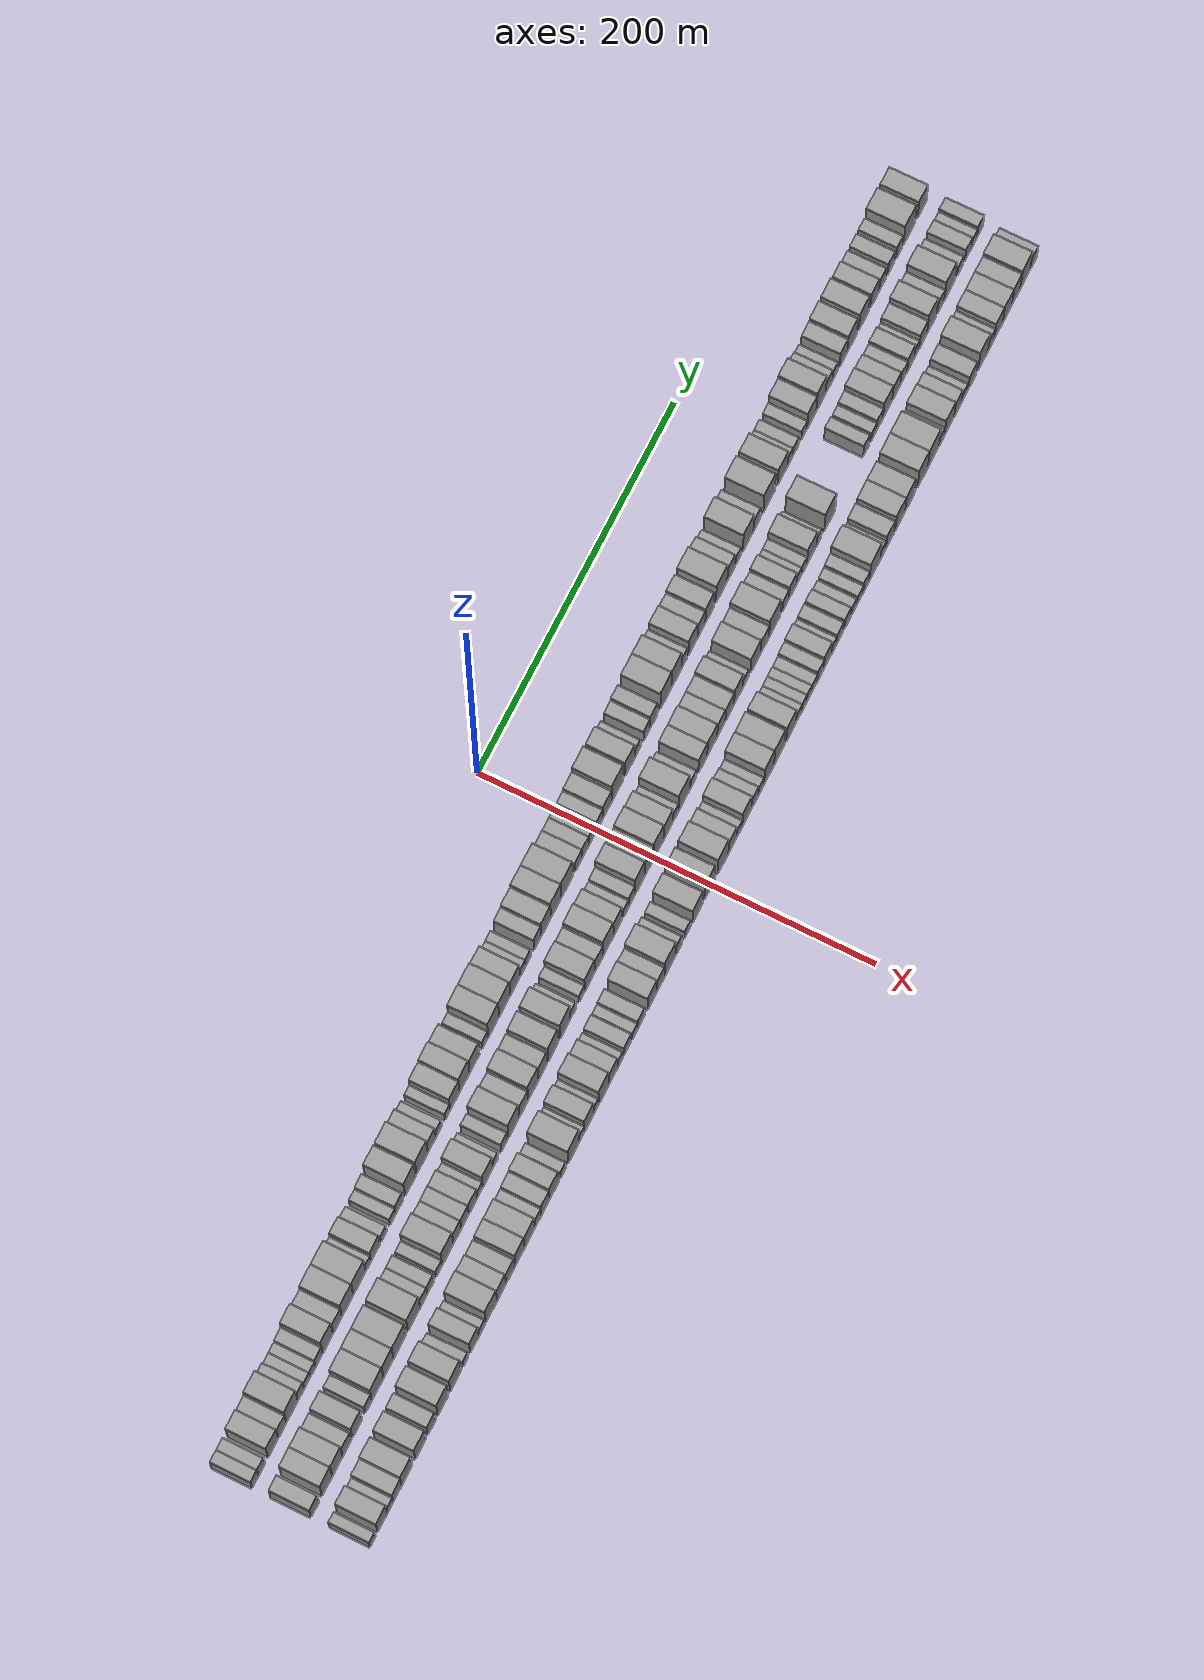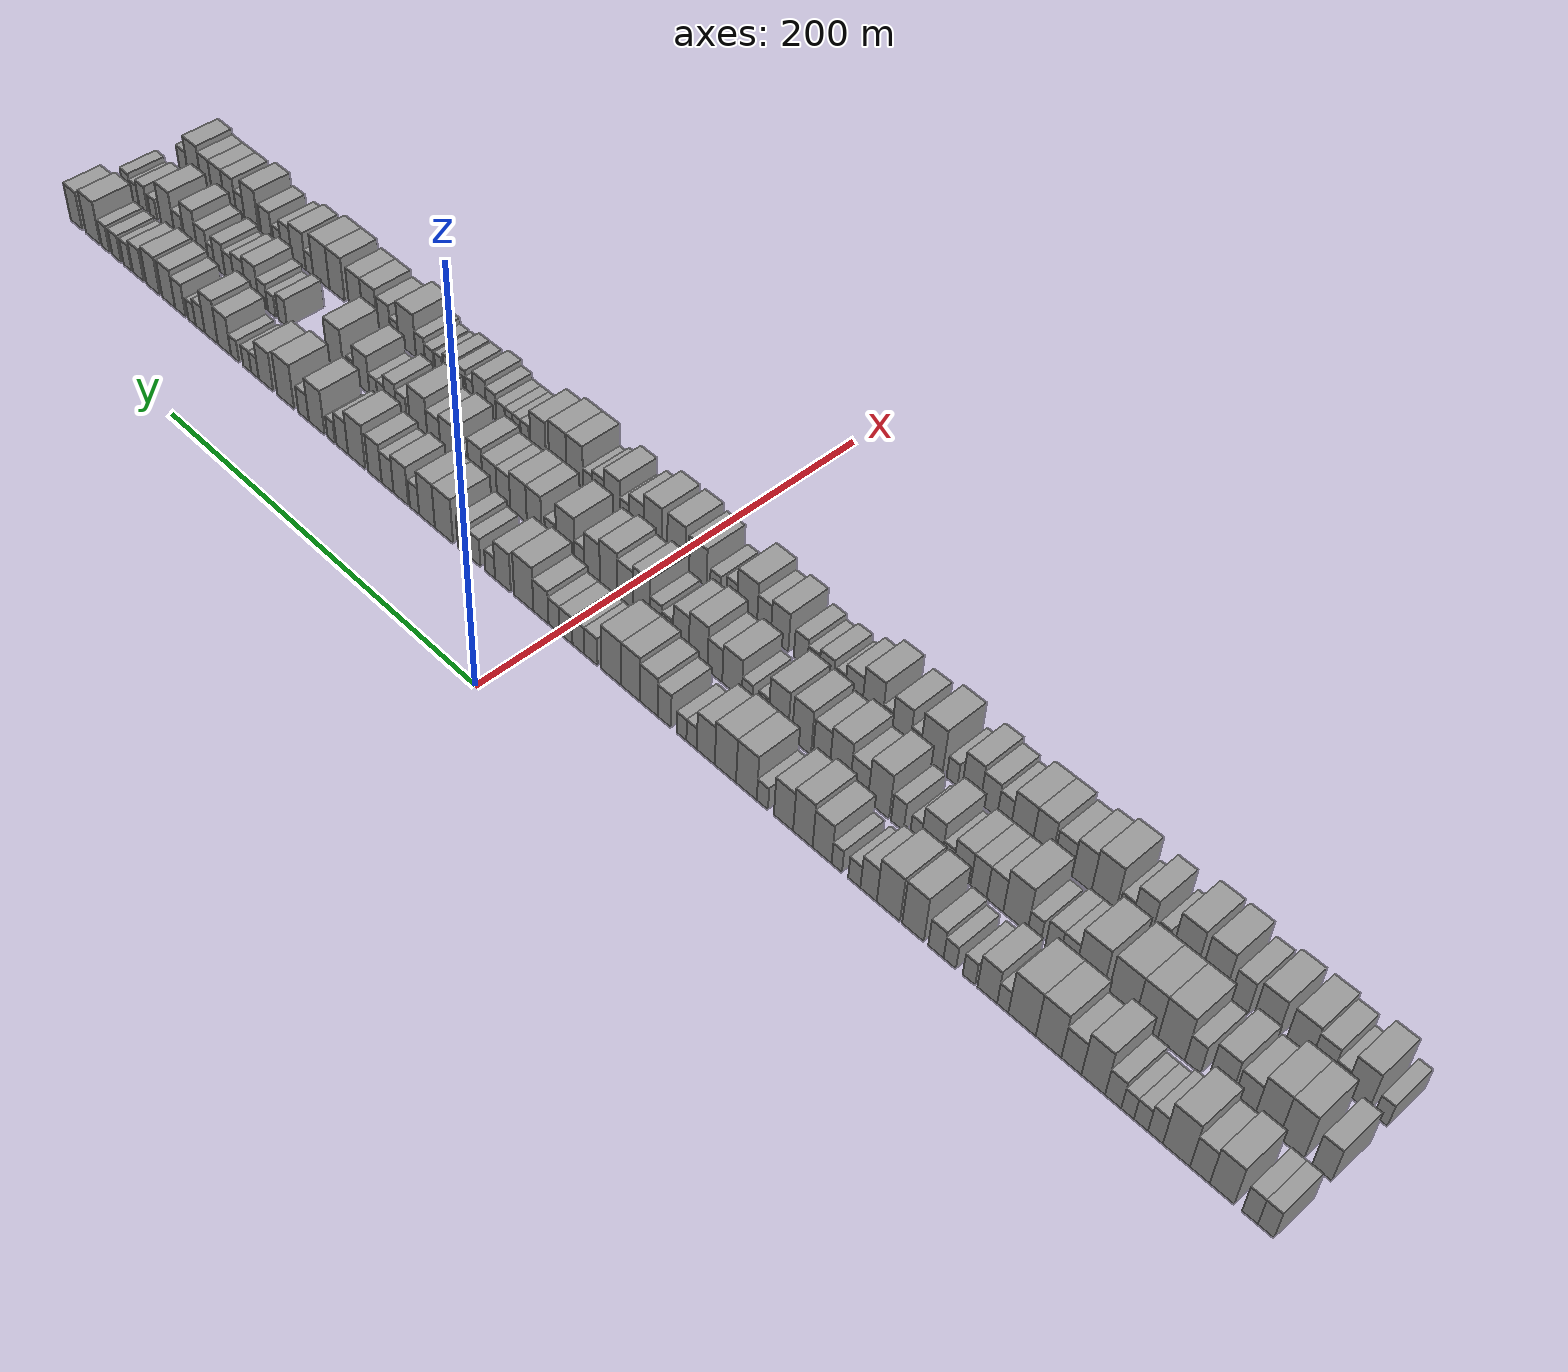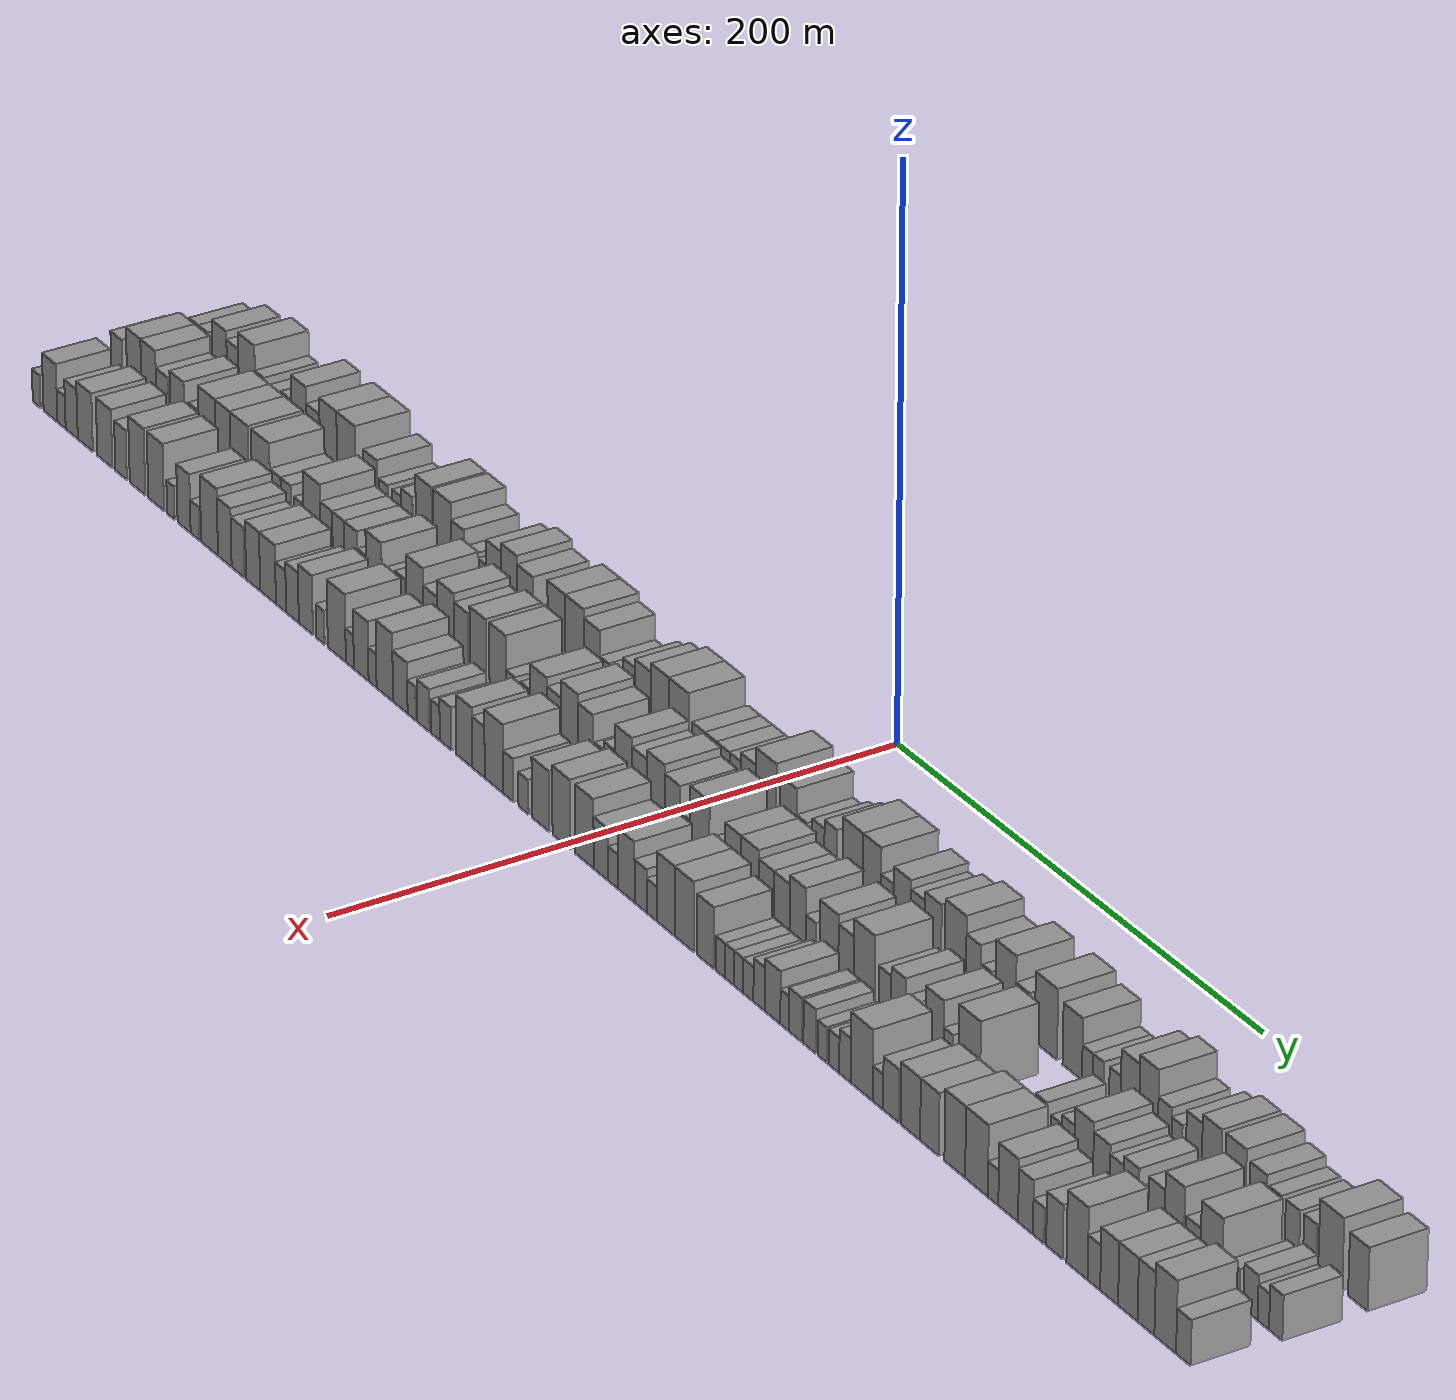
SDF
<sdf version="1.6">
 <world name="default">
  <scene>
   <sky><clouds><speed>12</speed></clouds></sky>
   <ambient>0.4 0.4 0.4 1</ambient>
   <background>0.7 0.7 0.7 1</background>
   <shadows>1</shadows>
  </scene>
  <gravity>0 0 -9.8066</gravity>
  <magnetic_field>6e-06 2.3e-05 -4.2e-05</magnetic_field>
  <physics default="0" name="default_physics" type="ode">
   <ode>
    <solver>
     <type>quick</type>
     <iters>10</iters>
     <sor>1.0</sor>
     <use_dynamic_moi_rescaling>0</use_dynamic_moi_rescaling>
    </solver>
    <constraints>
     <cfm>0</cfm>
     <erp>0.2</erp>
     <contact_max_correcting_vel>100</contact_max_correcting_vel>
     <contact_surface_layer>0.001</contact_surface_layer>
    </constraints>
   </ode>
   <max_step_size>0.004</max_step_size>
   <real_time_factor>1</real_time_factor>
   <real_time_update_rate>250</real_time_update_rate>
  </physics>
  <light name="sun" type="directional">
   <pose>0 0 10 0 0 0</pose>
   <diffuse>0.8 0.8 0.8 1</diffuse>
   <specular>0.2 0.2 0.2 1</specular>
   <attenuation>
    <range>1000</range>
    <constant>0.9</constant>
    <linear>0.01</linear>
    <quadratic>0.001</quadratic>
   </attenuation>
   <direction>-0.5 0.1 -0.9</direction>
  </light>
  <model name="building_1">
   <static>1</static>
   <pose>50.0000 -332.9100 0 0.000000 0.000000 0.000000</pose>
   <link name="link">
    <pose>0 0 7.50 0 0 0</pose>
    <collision name="collision"><geometry><box><size>20.0000 6.1801 15.0000</size></box></geometry></collision>
    <visual name="visual">
     <cast_shadows>0</cast_shadows>
     <geometry><box><size>20.0000 6.1801 15.0000</size></box></geometry>
     <material>
      <script>
       <uri>model://grey_wall/materials/scripts</uri>
       <uri>model://grey_wall/materials/textures</uri>
       <name>vrc/grey_wall</name>
      </script>
     </material>
    </visual>
   </link>
  </model>
  <model name="building_2">
   <static>1</static>
   <pose>50.0000 -326.7911 0 0.000000 0.000000 0.000000</pose>
   <link name="link">
    <pose>0 0 7.50 0 0 0</pose>
    <collision name="collision"><geometry><box><size>20.0000 6.0576 15.0000</size></box></geometry></collision>
    <visual name="visual">
     <cast_shadows>0</cast_shadows>
     <geometry><box><size>20.0000 6.0576 15.0000</size></box></geometry>
     <material>
      <script>
       <uri>model://grey_wall/materials/scripts</uri>
       <uri>model://grey_wall/materials/textures</uri>
       <name>vrc/grey_wall</name>
      </script>
     </material>
    </visual>
   </link>
  </model>
  <model name="building_3">
   <static>1</static>
   <pose>50.0000 -315.9852 0 0.000000 0.000000 0.000000</pose>
   <link name="link">
    <pose>0 0 10.50 0 0 0</pose>
    <collision name="collision"><geometry><box><size>20.0000 9.5543 21.0000</size></box></geometry></collision>
    <visual name="visual">
     <cast_shadows>0</cast_shadows>
     <geometry><box><size>20.0000 9.5543 21.0000</size></box></geometry>
     <material>
      <script>
       <uri>model://grey_wall/materials/scripts</uri>
       <uri>model://grey_wall/materials/textures</uri>
       <name>vrc/grey_wall</name>
      </script>
     </material>
    </visual>
   </link>
  </model>
  <model name="building_4">
   <static>1</static>
   <pose>50.0000 -307.3368 0 0.000000 0.000000 0.000000</pose>
   <link name="link">
    <pose>0 0 9.00 0 0 0</pose>
    <collision name="collision"><geometry><box><size>20.0000 7.7426 18.0000</size></box></geometry></collision>
    <visual name="visual">
     <cast_shadows>0</cast_shadows>
     <geometry><box><size>20.0000 7.7426 18.0000</size></box></geometry>
     <material>
      <script>
       <uri>model://grey_wall/materials/scripts</uri>
       <uri>model://grey_wall/materials/textures</uri>
       <name>vrc/grey_wall</name>
      </script>
     </material>
    </visual>
   </link>
  </model>
  <model name="building_5">
   <static>1</static>
   <pose>50.0000 -298.0444 0 0.000000 0.000000 0.000000</pose>
   <link name="link">
    <pose>0 0 12.00 0 0 0</pose>
    <collision name="collision"><geometry><box><size>20.0000 10.8422 24.0000</size></box></geometry></collision>
    <visual name="visual">
     <cast_shadows>0</cast_shadows>
     <geometry><box><size>20.0000 10.8422 24.0000</size></box></geometry>
     <material>
      <script>
       <uri>model://grey_wall/materials/scripts</uri>
       <uri>model://grey_wall/materials/textures</uri>
       <name>vrc/grey_wall</name>
      </script>
     </material>
    </visual>
   </link>
  </model>
  <model name="building_6">
   <static>1</static>
   <pose>50.0000 -289.6141 0 0.000000 0.000000 0.000000</pose>
   <link name="link">
    <pose>0 0 7.50 0 0 0</pose>
    <collision name="collision"><geometry><box><size>20.0000 6.0184 15.0000</size></box></geometry></collision>
    <visual name="visual">
     <cast_shadows>0</cast_shadows>
     <geometry><box><size>20.0000 6.0184 15.0000</size></box></geometry>
     <material>
      <script>
       <uri>model://grey_wall/materials/scripts</uri>
       <uri>model://grey_wall/materials/textures</uri>
       <name>vrc/grey_wall</name>
      </script>
     </material>
    </visual>
   </link>
  </model>
  <model name="building_7">
   <static>1</static>
   <pose>50.0000 -283.7388 0 0.000000 0.000000 0.000000</pose>
   <link name="link">
    <pose>0 0 6.00 0 0 0</pose>
    <collision name="collision"><geometry><box><size>20.0000 5.7323 12.0000</size></box></geometry></collision>
    <visual name="visual">
     <cast_shadows>0</cast_shadows>
     <geometry><box><size>20.0000 5.7323 12.0000</size></box></geometry>
     <material>
      <script>
       <uri>model://grey_wall/materials/scripts</uri>
       <uri>model://grey_wall/materials/textures</uri>
       <name>vrc/grey_wall</name>
      </script>
     </material>
    </visual>
   </link>
  </model>
  <model name="building_8">
   <static>1</static>
   <pose>50.0000 -278.2686 0 0.000000 0.000000 0.000000</pose>
   <link name="link">
    <pose>0 0 6.00 0 0 0</pose>
    <collision name="collision"><geometry><box><size>20.0000 5.2081 12.0000</size></box></geometry></collision>
    <visual name="visual">
     <cast_shadows>0</cast_shadows>
     <geometry><box><size>20.0000 5.2081 12.0000</size></box></geometry>
     <material>
      <script>
       <uri>model://grey_wall/materials/scripts</uri>
       <uri>model://grey_wall/materials/textures</uri>
       <name>vrc/grey_wall</name>
      </script>
     </material>
    </visual>
   </link>
  </model>
  <model name="building_9">
   <static>1</static>
   <pose>50.0000 -272.3338 0 0.000000 0.000000 0.000000</pose>
   <link name="link">
    <pose>0 0 7.50 0 0 0</pose>
    <collision name="collision"><geometry><box><size>20.0000 6.6615 15.0000</size></box></geometry></collision>
    <visual name="visual">
     <cast_shadows>0</cast_shadows>
     <geometry><box><size>20.0000 6.6615 15.0000</size></box></geometry>
     <material>
      <script>
       <uri>model://grey_wall/materials/scripts</uri>
       <uri>model://grey_wall/materials/textures</uri>
       <name>vrc/grey_wall</name>
      </script>
     </material>
    </visual>
   </link>
  </model>
  <model name="building_10">
   <static>1</static>
   <pose>50.0000 -264.0705 0 0.000000 0.000000 0.000000</pose>
   <link name="link">
    <pose>0 0 12.00 0 0 0</pose>
    <collision name="collision"><geometry><box><size>20.0000 9.8651 24.0000</size></box></geometry></collision>
    <visual name="visual">
     <cast_shadows>0</cast_shadows>
     <geometry><box><size>20.0000 9.8651 24.0000</size></box></geometry>
     <material>
      <script>
       <uri>model://grey_wall/materials/scripts</uri>
       <uri>model://grey_wall/materials/textures</uri>
       <name>vrc/grey_wall</name>
      </script>
     </material>
    </visual>
   </link>
  </model>
  <model name="building_11">
   <static>1</static>
   <pose>50.0000 -254.8802 0 0.000000 0.000000 0.000000</pose>
   <link name="link">
    <pose>0 0 9.00 0 0 0</pose>
    <collision name="collision"><geometry><box><size>20.0000 8.5157 18.0000</size></box></geometry></collision>
    <visual name="visual">
     <cast_shadows>0</cast_shadows>
     <geometry><box><size>20.0000 8.5157 18.0000</size></box></geometry>
     <material>
      <script>
       <uri>model://grey_wall/materials/scripts</uri>
       <uri>model://grey_wall/materials/textures</uri>
       <name>vrc/grey_wall</name>
      </script>
     </material>
    </visual>
   </link>
  </model>
  <model name="building_12">
   <static>1</static>
   <pose>50.0000 -245.1258 0 0.000000 0.000000 0.000000</pose>
   <link name="link">
    <pose>0 0 12.00 0 0 0</pose>
    <collision name="collision"><geometry><box><size>20.0000 10.9930 24.0000</size></box></geometry></collision>
    <visual name="visual">
     <cast_shadows>0</cast_shadows>
     <geometry><box><size>20.0000 10.9930 24.0000</size></box></geometry>
     <material>
      <script>
       <uri>model://grey_wall/materials/scripts</uri>
       <uri>model://grey_wall/materials/textures</uri>
       <name>vrc/grey_wall</name>
      </script>
     </material>
    </visual>
   </link>
  </model>
  <model name="building_13">
   <static>1</static>
   <pose>50.0000 -233.6606 0 0.000000 0.000000 0.000000</pose>
   <link name="link">
    <pose>0 0 12.00 0 0 0</pose>
    <collision name="collision"><geometry><box><size>20.0000 11.9374 24.0000</size></box></geometry></collision>
    <visual name="visual">
     <cast_shadows>0</cast_shadows>
     <geometry><box><size>20.0000 11.9374 24.0000</size></box></geometry>
     <material>
      <script>
       <uri>model://grey_wall/materials/scripts</uri>
       <uri>model://grey_wall/materials/textures</uri>
       <name>vrc/grey_wall</name>
      </script>
     </material>
    </visual>
   </link>
  </model>
  <model name="building_14">
   <static>1</static>
   <pose>50.0000 -225.2074 0 0.000000 0.000000 0.000000</pose>
   <link name="link">
    <pose>0 0 6.00 0 0 0</pose>
    <collision name="collision"><geometry><box><size>20.0000 4.9690 12.0000</size></box></geometry></collision>
    <visual name="visual">
     <cast_shadows>0</cast_shadows>
     <geometry><box><size>20.0000 4.9690 12.0000</size></box></geometry>
     <material>
      <script>
       <uri>model://grey_wall/materials/scripts</uri>
       <uri>model://grey_wall/materials/textures</uri>
       <name>vrc/grey_wall</name>
      </script>
     </material>
    </visual>
   </link>
  </model>
  <model name="building_15">
   <static>1</static>
   <pose>50.0000 -218.3566 0 0.000000 0.000000 0.000000</pose>
   <link name="link">
    <pose>0 0 9.00 0 0 0</pose>
    <collision name="collision"><geometry><box><size>20.0000 8.7326 18.0000</size></box></geometry></collision>
    <visual name="visual">
     <cast_shadows>0</cast_shadows>
     <geometry><box><size>20.0000 8.7326 18.0000</size></box></geometry>
     <material>
      <script>
       <uri>model://grey_wall/materials/scripts</uri>
       <uri>model://grey_wall/materials/textures</uri>
       <name>vrc/grey_wall</name>
      </script>
     </material>
    </visual>
   </link>
  </model>
  <model name="building_16">
   <static>1</static>
   <pose>50.0000 -210.1730 0 0.000000 0.000000 0.000000</pose>
   <link name="link">
    <pose>0 0 6.00 0 0 0</pose>
    <collision name="collision"><geometry><box><size>20.0000 5.6346 12.0000</size></box></geometry></collision>
    <visual name="visual">
     <cast_shadows>0</cast_shadows>
     <geometry><box><size>20.0000 5.6346 12.0000</size></box></geometry>
     <material>
      <script>
       <uri>model://grey_wall/materials/scripts</uri>
       <uri>model://grey_wall/materials/textures</uri>
       <name>vrc/grey_wall</name>
      </script>
     </material>
    </visual>
   </link>
  </model>
  <model name="building_17">
   <static>1</static>
   <pose>50.0000 -201.5281 0 0.000000 0.000000 0.000000</pose>
   <link name="link">
    <pose>0 0 6.00 0 0 0</pose>
    <collision name="collision"><geometry><box><size>20.0000 5.6551 12.0000</size></box></geometry></collision>
    <visual name="visual">
     <cast_shadows>0</cast_shadows>
     <geometry><box><size>20.0000 5.6551 12.0000</size></box></geometry>
     <material>
      <script>
       <uri>model://grey_wall/materials/scripts</uri>
       <uri>model://grey_wall/materials/textures</uri>
       <name>vrc/grey_wall</name>
      </script>
     </material>
    </visual>
   </link>
  </model>
  <model name="building_18">
   <static>1</static>
   <pose>50.0000 -195.1755 0 0.000000 0.000000 0.000000</pose>
   <link name="link">
    <pose>0 0 7.50 0 0 0</pose>
    <collision name="collision"><geometry><box><size>20.0000 7.0502 15.0000</size></box></geometry></collision>
    <visual name="visual">
     <cast_shadows>0</cast_shadows>
     <geometry><box><size>20.0000 7.0502 15.0000</size></box></geometry>
     <material>
      <script>
       <uri>model://grey_wall/materials/scripts</uri>
       <uri>model://grey_wall/materials/textures</uri>
       <name>vrc/grey_wall</name>
      </script>
     </material>
    </visual>
   </link>
  </model>
  <model name="building_19">
   <static>1</static>
   <pose>50.0000 -184.6039 0 0.000000 0.000000 0.000000</pose>
   <link name="link">
    <pose>0 0 12.00 0 0 0</pose>
    <collision name="collision"><geometry><box><size>20.0000 10.0929 24.0000</size></box></geometry></collision>
    <visual name="visual">
     <cast_shadows>0</cast_shadows>
     <geometry><box><size>20.0000 10.0929 24.0000</size></box></geometry>
     <material>
      <script>
       <uri>model://grey_wall/materials/scripts</uri>
       <uri>model://grey_wall/materials/textures</uri>
       <name>vrc/grey_wall</name>
      </script>
     </material>
    </visual>
   </link>
  </model>
  <model name="building_20">
   <static>1</static>
   <pose>50.0000 -173.0577 0 0.000000 0.000000 0.000000</pose>
   <link name="link">
    <pose>0 0 12.00 0 0 0</pose>
    <collision name="collision"><geometry><box><size>20.0000 10.9995 24.0000</size></box></geometry></collision>
    <visual name="visual">
     <cast_shadows>0</cast_shadows>
     <geometry><box><size>20.0000 10.9995 24.0000</size></box></geometry>
     <material>
      <script>
       <uri>model://grey_wall/materials/scripts</uri>
       <uri>model://grey_wall/materials/textures</uri>
       <name>vrc/grey_wall</name>
      </script>
     </material>
    </visual>
   </link>
  </model>
  <model name="building_21">
   <static>1</static>
   <pose>50.0000 -163.6512 0 0.000000 0.000000 0.000000</pose>
   <link name="link">
    <pose>0 0 9.00 0 0 0</pose>
    <collision name="collision"><geometry><box><size>20.0000 7.8137 18.0000</size></box></geometry></collision>
    <visual name="visual">
     <cast_shadows>0</cast_shadows>
     <geometry><box><size>20.0000 7.8137 18.0000</size></box></geometry>
     <material>
      <script>
       <uri>model://grey_wall/materials/scripts</uri>
       <uri>model://grey_wall/materials/textures</uri>
       <name>vrc/grey_wall</name>
      </script>
     </material>
    </visual>
   </link>
  </model>
  <model name="building_22">
   <static>1</static>
   <pose>50.0000 -156.8020 0 0.000000 0.000000 0.000000</pose>
   <link name="link">
    <pose>0 0 6.00 0 0 0</pose>
    <collision name="collision"><geometry><box><size>20.0000 5.8847 12.0000</size></box></geometry></collision>
    <visual name="visual">
     <cast_shadows>0</cast_shadows>
     <geometry><box><size>20.0000 5.8847 12.0000</size></box></geometry>
     <material>
      <script>
       <uri>model://grey_wall/materials/scripts</uri>
       <uri>model://grey_wall/materials/textures</uri>
       <name>vrc/grey_wall</name>
      </script>
     </material>
    </visual>
   </link>
  </model>
  <model name="building_23">
   <static>1</static>
   <pose>50.0000 -148.3173 0 0.000000 0.000000 0.000000</pose>
   <link name="link">
    <pose>0 0 6.00 0 0 0</pose>
    <collision name="collision"><geometry><box><size>20.0000 5.0847 12.0000</size></box></geometry></collision>
    <visual name="visual">
     <cast_shadows>0</cast_shadows>
     <geometry><box><size>20.0000 5.0847 12.0000</size></box></geometry>
     <material>
      <script>
       <uri>model://grey_wall/materials/scripts</uri>
       <uri>model://grey_wall/materials/textures</uri>
       <name>vrc/grey_wall</name>
      </script>
     </material>
    </visual>
   </link>
  </model>
  <model name="building_24">
   <static>1</static>
   <pose>50.0000 -141.1029 0 0.000000 0.000000 0.000000</pose>
   <link name="link">
    <pose>0 0 10.50 0 0 0</pose>
    <collision name="collision"><geometry><box><size>20.0000 9.3441 21.0000</size></box></geometry></collision>
    <visual name="visual">
     <cast_shadows>0</cast_shadows>
     <geometry><box><size>20.0000 9.3441 21.0000</size></box></geometry>
     <material>
      <script>
       <uri>model://grey_wall/materials/scripts</uri>
       <uri>model://grey_wall/materials/textures</uri>
       <name>vrc/grey_wall</name>
      </script>
     </material>
    </visual>
   </link>
  </model>
  <model name="building_25">
   <static>1</static>
   <pose>50.0000 -131.5984 0 0.000000 0.000000 0.000000</pose>
   <link name="link">
    <pose>0 0 12.00 0 0 0</pose>
    <collision name="collision"><geometry><box><size>20.0000 9.6648 24.0000</size></box></geometry></collision>
    <visual name="visual">
     <cast_shadows>0</cast_shadows>
     <geometry><box><size>20.0000 9.6648 24.0000</size></box></geometry>
     <material>
      <script>
       <uri>model://grey_wall/materials/scripts</uri>
       <uri>model://grey_wall/materials/textures</uri>
       <name>vrc/grey_wall</name>
      </script>
     </material>
    </visual>
   </link>
  </model>
  <model name="building_26">
   <static>1</static>
   <pose>50.0000 -121.9119 0 0.000000 0.000000 0.000000</pose>
   <link name="link">
    <pose>0 0 10.50 0 0 0</pose>
    <collision name="collision"><geometry><box><size>20.0000 9.7083 21.0000</size></box></geometry></collision>
    <visual name="visual">
     <cast_shadows>0</cast_shadows>
     <geometry><box><size>20.0000 9.7083 21.0000</size></box></geometry>
     <material>
      <script>
       <uri>model://grey_wall/materials/scripts</uri>
       <uri>model://grey_wall/materials/textures</uri>
       <name>vrc/grey_wall</name>
      </script>
     </material>
    </visual>
   </link>
  </model>
  <model name="building_27">
   <static>1</static>
   <pose>50.0000 -111.1926 0 0.000000 0.000000 0.000000</pose>
   <link name="link">
    <pose>0 0 6.00 0 0 0</pose>
    <collision name="collision"><geometry><box><size>20.0000 5.7304 12.0000</size></box></geometry></collision>
    <visual name="visual">
     <cast_shadows>0</cast_shadows>
     <geometry><box><size>20.0000 5.7304 12.0000</size></box></geometry>
     <material>
      <script>
       <uri>model://grey_wall/materials/scripts</uri>
       <uri>model://grey_wall/materials/textures</uri>
       <name>vrc/grey_wall</name>
      </script>
     </material>
    </visual>
   </link>
  </model>
  <model name="building_28">
   <static>1</static>
   <pose>50.0000 -102.9746 0 0.000000 0.000000 0.000000</pose>
   <link name="link">
    <pose>0 0 12.00 0 0 0</pose>
    <collision name="collision"><geometry><box><size>20.0000 10.7056 24.0000</size></box></geometry></collision>
    <visual name="visual">
     <cast_shadows>0</cast_shadows>
     <geometry><box><size>20.0000 10.7056 24.0000</size></box></geometry>
     <material>
      <script>
       <uri>model://grey_wall/materials/scripts</uri>
       <uri>model://grey_wall/materials/textures</uri>
       <name>vrc/grey_wall</name>
      </script>
     </material>
    </visual>
   </link>
  </model>
  <model name="building_29">
   <static>1</static>
   <pose>50.0000 -92.0782 0 0.000000 0.000000 0.000000</pose>
   <link name="link">
    <pose>0 0 12.00 0 0 0</pose>
    <collision name="collision"><geometry><box><size>20.0000 11.0870 24.0000</size></box></geometry></collision>
    <visual name="visual">
     <cast_shadows>0</cast_shadows>
     <geometry><box><size>20.0000 11.0870 24.0000</size></box></geometry>
     <material>
      <script>
       <uri>model://grey_wall/materials/scripts</uri>
       <uri>model://grey_wall/materials/textures</uri>
       <name>vrc/grey_wall</name>
      </script>
     </material>
    </visual>
   </link>
  </model>
  <model name="building_30">
   <static>1</static>
   <pose>50.0000 -81.7532 0 0.000000 0.000000 0.000000</pose>
   <link name="link">
    <pose>0 0 10.50 0 0 0</pose>
    <collision name="collision"><geometry><box><size>20.0000 9.5631 21.0000</size></box></geometry></collision>
    <visual name="visual">
     <cast_shadows>0</cast_shadows>
     <geometry><box><size>20.0000 9.5631 21.0000</size></box></geometry>
     <material>
      <script>
       <uri>model://grey_wall/materials/scripts</uri>
       <uri>model://grey_wall/materials/textures</uri>
       <name>vrc/grey_wall</name>
      </script>
     </material>
    </visual>
   </link>
  </model>
  <model name="building_31">
   <static>1</static>
   <pose>50.0000 -74.2111 0 0.000000 0.000000 0.000000</pose>
   <link name="link">
    <pose>0 0 6.00 0 0 0</pose>
    <collision name="collision"><geometry><box><size>20.0000 5.5211 12.0000</size></box></geometry></collision>
    <visual name="visual">
     <cast_shadows>0</cast_shadows>
     <geometry><box><size>20.0000 5.5211 12.0000</size></box></geometry>
     <material>
      <script>
       <uri>model://grey_wall/materials/scripts</uri>
       <uri>model://grey_wall/materials/textures</uri>
       <name>vrc/grey_wall</name>
      </script>
     </material>
    </visual>
   </link>
  </model>
  <model name="building_32">
   <static>1</static>
   <pose>50.0000 -68.8047 0 0.000000 0.000000 0.000000</pose>
   <link name="link">
    <pose>0 0 6.00 0 0 0</pose>
    <collision name="collision"><geometry><box><size>20.0000 5.2918 12.0000</size></box></geometry></collision>
    <visual name="visual">
     <cast_shadows>0</cast_shadows>
     <geometry><box><size>20.0000 5.2918 12.0000</size></box></geometry>
     <material>
      <script>
       <uri>model://grey_wall/materials/scripts</uri>
       <uri>model://grey_wall/materials/textures</uri>
       <name>vrc/grey_wall</name>
      </script>
     </material>
    </visual>
   </link>
  </model>
  <model name="building_33">
   <static>1</static>
   <pose>50.0000 -59.5514 0 0.000000 0.000000 0.000000</pose>
   <link name="link">
    <pose>0 0 9.00 0 0 0</pose>
    <collision name="collision"><geometry><box><size>20.0000 7.2146 18.0000</size></box></geometry></collision>
    <visual name="visual">
     <cast_shadows>0</cast_shadows>
     <geometry><box><size>20.0000 7.2146 18.0000</size></box></geometry>
     <material>
      <script>
       <uri>model://grey_wall/materials/scripts</uri>
       <uri>model://grey_wall/materials/textures</uri>
       <name>vrc/grey_wall</name>
      </script>
     </material>
    </visual>
   </link>
  </model>
  <model name="building_34">
   <static>1</static>
   <pose>50.0000 -51.1567 0 0.000000 0.000000 0.000000</pose>
   <link name="link">
    <pose>0 0 10.50 0 0 0</pose>
    <collision name="collision"><geometry><box><size>20.0000 9.5748 21.0000</size></box></geometry></collision>
    <visual name="visual">
     <cast_shadows>0</cast_shadows>
     <geometry><box><size>20.0000 9.5748 21.0000</size></box></geometry>
     <material>
      <script>
       <uri>model://grey_wall/materials/scripts</uri>
       <uri>model://grey_wall/materials/textures</uri>
       <name>vrc/grey_wall</name>
      </script>
     </material>
    </visual>
   </link>
  </model>
  <model name="building_35">
   <static>1</static>
   <pose>50.0000 -41.1440 0 0.000000 0.000000 0.000000</pose>
   <link name="link">
    <pose>0 0 12.00 0 0 0</pose>
    <collision name="collision"><geometry><box><size>20.0000 10.4507 24.0000</size></box></geometry></collision>
    <visual name="visual">
     <cast_shadows>0</cast_shadows>
     <geometry><box><size>20.0000 10.4507 24.0000</size></box></geometry>
     <material>
      <script>
       <uri>model://grey_wall/materials/scripts</uri>
       <uri>model://grey_wall/materials/textures</uri>
       <name>vrc/grey_wall</name>
      </script>
     </material>
    </visual>
   </link>
  </model>
  <model name="building_36">
   <static>1</static>
   <pose>50.0000 -30.1692 0 0.000000 0.000000 0.000000</pose>
   <link name="link">
    <pose>0 0 12.00 0 0 0</pose>
    <collision name="collision"><geometry><box><size>20.0000 11.4988 24.0000</size></box></geometry></collision>
    <visual name="visual">
     <cast_shadows>0</cast_shadows>
     <geometry><box><size>20.0000 11.4988 24.0000</size></box></geometry>
     <material>
      <script>
       <uri>model://grey_wall/materials/scripts</uri>
       <uri>model://grey_wall/materials/textures</uri>
       <name>vrc/grey_wall</name>
      </script>
     </material>
    </visual>
   </link>
  </model>
  <model name="building_37">
   <static>1</static>
   <pose>50.0000 -18.6706 0 0.000000 0.000000 0.000000</pose>
   <link name="link">
    <pose>0 0 7.50 0 0 0</pose>
    <collision name="collision"><geometry><box><size>20.0000 7.4985 15.0000</size></box></geometry></collision>
    <visual name="visual">
     <cast_shadows>0</cast_shadows>
     <geometry><box><size>20.0000 7.4985 15.0000</size></box></geometry>
     <material>
      <script>
       <uri>model://grey_wall/materials/scripts</uri>
       <uri>model://grey_wall/materials/textures</uri>
       <name>vrc/grey_wall</name>
      </script>
     </material>
    </visual>
   </link>
  </model>
  <model name="building_38">
   <static>1</static>
   <pose>50.0000 -11.4941 0 0.000000 0.000000 0.000000</pose>
   <link name="link">
    <pose>0 0 7.50 0 0 0</pose>
    <collision name="collision"><geometry><box><size>20.0000 6.8543 15.0000</size></box></geometry></collision>
    <visual name="visual">
     <cast_shadows>0</cast_shadows>
     <geometry><box><size>20.0000 6.8543 15.0000</size></box></geometry>
     <material>
      <script>
       <uri>model://grey_wall/materials/scripts</uri>
       <uri>model://grey_wall/materials/textures</uri>
       <name>vrc/grey_wall</name>
      </script>
     </material>
    </visual>
   </link>
  </model>
  <model name="building_39">
   <static>1</static>
   <pose>50.0000 -4.3463 0 0.000000 0.000000 0.000000</pose>
   <link name="link">
    <pose>0 0 7.50 0 0 0</pose>
    <collision name="collision"><geometry><box><size>20.0000 7.4413 15.0000</size></box></geometry></collision>
    <visual name="visual">
     <cast_shadows>0</cast_shadows>
     <geometry><box><size>20.0000 7.4413 15.0000</size></box></geometry>
     <material>
      <script>
       <uri>model://grey_wall/materials/scripts</uri>
       <uri>model://grey_wall/materials/textures</uri>
       <name>vrc/grey_wall</name>
      </script>
     </material>
    </visual>
   </link>
  </model>
  <model name="building_40">
   <static>1</static>
   <pose>50.0000 2.6433 0 0.000000 0.000000 0.000000</pose>
   <link name="link">
    <pose>0 0 7.50 0 0 0</pose>
    <collision name="collision"><geometry><box><size>20.0000 6.5380 15.0000</size></box></geometry></collision>
    <visual name="visual">
     <cast_shadows>0</cast_shadows>
     <geometry><box><size>20.0000 6.5380 15.0000</size></box></geometry>
     <material>
      <script>
       <uri>model://grey_wall/materials/scripts</uri>
       <uri>model://grey_wall/materials/textures</uri>
       <name>vrc/grey_wall</name>
      </script>
     </material>
    </visual>
   </link>
  </model>
  <model name="building_41">
   <static>1</static>
   <pose>50.0000 10.3555 0 0.000000 0.000000 0.000000</pose>
   <link name="link">
    <pose>0 0 9.00 0 0 0</pose>
    <collision name="collision"><geometry><box><size>20.0000 8.8864 18.0000</size></box></geometry></collision>
    <visual name="visual">
     <cast_shadows>0</cast_shadows>
     <geometry><box><size>20.0000 8.8864 18.0000</size></box></geometry>
     <material>
      <script>
       <uri>model://grey_wall/materials/scripts</uri>
       <uri>model://grey_wall/materials/textures</uri>
       <name>vrc/grey_wall</name>
      </script>
     </material>
    </visual>
   </link>
  </model>
  <model name="building_42">
   <static>1</static>
   <pose>50.0000 20.5644 0 0.000000 0.000000 0.000000</pose>
   <link name="link">
    <pose>0 0 12.00 0 0 0</pose>
    <collision name="collision"><geometry><box><size>20.0000 11.5315 24.0000</size></box></geometry></collision>
    <visual name="visual">
     <cast_shadows>0</cast_shadows>
     <geometry><box><size>20.0000 11.5315 24.0000</size></box></geometry>
     <material>
      <script>
       <uri>model://grey_wall/materials/scripts</uri>
       <uri>model://grey_wall/materials/textures</uri>
       <name>vrc/grey_wall</name>
      </script>
     </material>
    </visual>
   </link>
  </model>
  <model name="building_43">
   <static>1</static>
   <pose>50.0000 33.1167 0 0.000000 0.000000 0.000000</pose>
   <link name="link">
    <pose>0 0 10.50 0 0 0</pose>
    <collision name="collision"><geometry><box><size>20.0000 9.5731 21.0000</size></box></geometry></collision>
    <visual name="visual">
     <cast_shadows>0</cast_shadows>
     <geometry><box><size>20.0000 9.5731 21.0000</size></box></geometry>
     <material>
      <script>
       <uri>model://grey_wall/materials/scripts</uri>
       <uri>model://grey_wall/materials/textures</uri>
       <name>vrc/grey_wall</name>
      </script>
     </material>
    </visual>
   </link>
  </model>
  <model name="building_44">
   <static>1</static>
   <pose>50.0000 40.8518 0 0.000000 0.000000 0.000000</pose>
   <link name="link">
    <pose>0 0 6.00 0 0 0</pose>
    <collision name="collision"><geometry><box><size>20.0000 5.8971 12.0000</size></box></geometry></collision>
    <visual name="visual">
     <cast_shadows>0</cast_shadows>
     <geometry><box><size>20.0000 5.8971 12.0000</size></box></geometry>
     <material>
      <script>
       <uri>model://grey_wall/materials/scripts</uri>
       <uri>model://grey_wall/materials/textures</uri>
       <name>vrc/grey_wall</name>
      </script>
     </material>
    </visual>
   </link>
  </model>
  <model name="building_45">
   <static>1</static>
   <pose>50.0000 50.2106 0 0.000000 0.000000 0.000000</pose>
   <link name="link">
    <pose>0 0 7.50 0 0 0</pose>
    <collision name="collision"><geometry><box><size>20.0000 6.8205 15.0000</size></box></geometry></collision>
    <visual name="visual">
     <cast_shadows>0</cast_shadows>
     <geometry><box><size>20.0000 6.8205 15.0000</size></box></geometry>
     <material>
      <script>
       <uri>model://grey_wall/materials/scripts</uri>
       <uri>model://grey_wall/materials/textures</uri>
       <name>vrc/grey_wall</name>
      </script>
     </material>
    </visual>
   </link>
  </model>
  <model name="building_46">
   <static>1</static>
   <pose>50.0000 57.2424 0 0.000000 0.000000 0.000000</pose>
   <link name="link">
    <pose>0 0 9.00 0 0 0</pose>
    <collision name="collision"><geometry><box><size>20.0000 7.2431 18.0000</size></box></geometry></collision>
    <visual name="visual">
     <cast_shadows>0</cast_shadows>
     <geometry><box><size>20.0000 7.2431 18.0000</size></box></geometry>
     <material>
      <script>
       <uri>model://grey_wall/materials/scripts</uri>
       <uri>model://grey_wall/materials/textures</uri>
       <name>vrc/grey_wall</name>
      </script>
     </material>
    </visual>
   </link>
  </model>
  <model name="building_47">
   <static>1</static>
   <pose>50.0000 69.6087 0 0.000000 0.000000 0.000000</pose>
   <link name="link">
    <pose>0 0 12.00 0 0 0</pose>
    <collision name="collision"><geometry><box><size>20.0000 11.4896 24.0000</size></box></geometry></collision>
    <visual name="visual">
     <cast_shadows>0</cast_shadows>
     <geometry><box><size>20.0000 11.4896 24.0000</size></box></geometry>
     <material>
      <script>
       <uri>model://grey_wall/materials/scripts</uri>
       <uri>model://grey_wall/materials/textures</uri>
       <name>vrc/grey_wall</name>
      </script>
     </material>
    </visual>
   </link>
  </model>
  <model name="building_48">
   <static>1</static>
   <pose>50.0000 80.3825 0 0.000000 0.000000 0.000000</pose>
   <link name="link">
    <pose>0 0 12.00 0 0 0</pose>
    <collision name="collision"><geometry><box><size>20.0000 10.0580 24.0000</size></box></geometry></collision>
    <visual name="visual">
     <cast_shadows>0</cast_shadows>
     <geometry><box><size>20.0000 10.0580 24.0000</size></box></geometry>
     <material>
      <script>
       <uri>model://grey_wall/materials/scripts</uri>
       <uri>model://grey_wall/materials/textures</uri>
       <name>vrc/grey_wall</name>
      </script>
     </material>
    </visual>
   </link>
  </model>
  <model name="building_49">
   <static>1</static>
   <pose>50.0000 88.4123 0 0.000000 0.000000 0.000000</pose>
   <link name="link">
    <pose>0 0 7.50 0 0 0</pose>
    <collision name="collision"><geometry><box><size>20.0000 6.0016 15.0000</size></box></geometry></collision>
    <visual name="visual">
     <cast_shadows>0</cast_shadows>
     <geometry><box><size>20.0000 6.0016 15.0000</size></box></geometry>
     <material>
      <script>
       <uri>model://grey_wall/materials/scripts</uri>
       <uri>model://grey_wall/materials/textures</uri>
       <name>vrc/grey_wall</name>
      </script>
     </material>
    </visual>
   </link>
  </model>
  <model name="building_50">
   <static>1</static>
   <pose>50.0000 97.2108 0 0.000000 0.000000 0.000000</pose>
   <link name="link">
    <pose>0 0 10.50 0 0 0</pose>
    <collision name="collision"><geometry><box><size>20.0000 9.5954 21.0000</size></box></geometry></collision>
    <visual name="visual">
     <cast_shadows>0</cast_shadows>
     <geometry><box><size>20.0000 9.5954 21.0000</size></box></geometry>
     <material>
      <script>
       <uri>model://grey_wall/materials/scripts</uri>
       <uri>model://grey_wall/materials/textures</uri>
       <name>vrc/grey_wall</name>
      </script>
     </material>
    </visual>
   </link>
  </model>
  <model name="building_51">
   <static>1</static>
   <pose>50.0000 105.8910 0 0.000000 0.000000 0.000000</pose>
   <link name="link">
    <pose>0 0 9.00 0 0 0</pose>
    <collision name="collision"><geometry><box><size>20.0000 7.7649 18.0000</size></box></geometry></collision>
    <visual name="visual">
     <cast_shadows>0</cast_shadows>
     <geometry><box><size>20.0000 7.7649 18.0000</size></box></geometry>
     <material>
      <script>
       <uri>model://grey_wall/materials/scripts</uri>
       <uri>model://grey_wall/materials/textures</uri>
       <name>vrc/grey_wall</name>
      </script>
     </material>
    </visual>
   </link>
  </model>
  <model name="building_52">
   <static>1</static>
   <pose>50.0000 114.2471 0 0.000000 0.000000 0.000000</pose>
   <link name="link">
    <pose>0 0 10.50 0 0 0</pose>
    <collision name="collision"><geometry><box><size>20.0000 8.9474 21.0000</size></box></geometry></collision>
    <visual name="visual">
     <cast_shadows>0</cast_shadows>
     <geometry><box><size>20.0000 8.9474 21.0000</size></box></geometry>
     <material>
      <script>
       <uri>model://grey_wall/materials/scripts</uri>
       <uri>model://grey_wall/materials/textures</uri>
       <name>vrc/grey_wall</name>
      </script>
     </material>
    </visual>
   </link>
  </model>
  <model name="building_53">
   <static>1</static>
   <pose>50.0000 126.5164 0 0.000000 0.000000 0.000000</pose>
   <link name="link">
    <pose>0 0 12.00 0 0 0</pose>
    <collision name="collision"><geometry><box><size>20.0000 11.5913 24.0000</size></box></geometry></collision>
    <visual name="visual">
     <cast_shadows>0</cast_shadows>
     <geometry><box><size>20.0000 11.5913 24.0000</size></box></geometry>
     <material>
      <script>
       <uri>model://grey_wall/materials/scripts</uri>
       <uri>model://grey_wall/materials/textures</uri>
       <name>vrc/grey_wall</name>
      </script>
     </material>
    </visual>
   </link>
  </model>
  <model name="building_54">
   <static>1</static>
   <pose>50.0000 136.2720 0 0.000000 0.000000 0.000000</pose>
   <link name="link">
    <pose>0 0 9.00 0 0 0</pose>
    <collision name="collision"><geometry><box><size>20.0000 7.9199 18.0000</size></box></geometry></collision>
    <visual name="visual">
     <cast_shadows>0</cast_shadows>
     <geometry><box><size>20.0000 7.9199 18.0000</size></box></geometry>
     <material>
      <script>
       <uri>model://grey_wall/materials/scripts</uri>
       <uri>model://grey_wall/materials/textures</uri>
       <name>vrc/grey_wall</name>
      </script>
     </material>
    </visual>
   </link>
  </model>
  <model name="building_55">
   <static>1</static>
   <pose>50.0000 143.8051 0 0.000000 0.000000 0.000000</pose>
   <link name="link">
    <pose>0 0 6.00 0 0 0</pose>
    <collision name="collision"><geometry><box><size>20.0000 5.1463 12.0000</size></box></geometry></collision>
    <visual name="visual">
     <cast_shadows>0</cast_shadows>
     <geometry><box><size>20.0000 5.1463 12.0000</size></box></geometry>
     <material>
      <script>
       <uri>model://grey_wall/materials/scripts</uri>
       <uri>model://grey_wall/materials/textures</uri>
       <name>vrc/grey_wall</name>
      </script>
     </material>
    </visual>
   </link>
  </model>
  <model name="building_56">
   <static>1</static>
   <pose>50.0000 153.8165 0 0.000000 0.000000 0.000000</pose>
   <link name="link">
    <pose>0 0 12.00 0 0 0</pose>
    <collision name="collision"><geometry><box><size>20.0000 10.8766 24.0000</size></box></geometry></collision>
    <visual name="visual">
     <cast_shadows>0</cast_shadows>
     <geometry><box><size>20.0000 10.8766 24.0000</size></box></geometry>
     <material>
      <script>
       <uri>model://grey_wall/materials/scripts</uri>
       <uri>model://grey_wall/materials/textures</uri>
       <name>vrc/grey_wall</name>
      </script>
     </material>
    </visual>
   </link>
  </model>
  <model name="building_57">
   <static>1</static>
   <pose>50.0000 162.9138 0 0.000000 0.000000 0.000000</pose>
   <link name="link">
    <pose>0 0 7.50 0 0 0</pose>
    <collision name="collision"><geometry><box><size>20.0000 7.3179 15.0000</size></box></geometry></collision>
    <visual name="visual">
     <cast_shadows>0</cast_shadows>
     <geometry><box><size>20.0000 7.3179 15.0000</size></box></geometry>
     <material>
      <script>
       <uri>model://grey_wall/materials/scripts</uri>
       <uri>model://grey_wall/materials/textures</uri>
       <name>vrc/grey_wall</name>
      </script>
     </material>
    </visual>
   </link>
  </model>
  <model name="building_58">
   <static>1</static>
   <pose>50.0000 175.5342 0 0.000000 0.000000 0.000000</pose>
   <link name="link">
    <pose>0 0 12.00 0 0 0</pose>
    <collision name="collision"><geometry><box><size>20.0000 11.9230 24.0000</size></box></geometry></collision>
    <visual name="visual">
     <cast_shadows>0</cast_shadows>
     <geometry><box><size>20.0000 11.9230 24.0000</size></box></geometry>
     <material>
      <script>
       <uri>model://grey_wall/materials/scripts</uri>
       <uri>model://grey_wall/materials/textures</uri>
       <name>vrc/grey_wall</name>
      </script>
     </material>
    </visual>
   </link>
  </model>
  <model name="building_59">
   <static>1</static>
   <pose>50.0000 189.6676 0 0.000000 0.000000 0.000000</pose>
   <link name="link">
    <pose>0 0 10.50 0 0 0</pose>
    <collision name="collision"><geometry><box><size>20.0000 10.3438 21.0000</size></box></geometry></collision>
    <visual name="visual">
     <cast_shadows>0</cast_shadows>
     <geometry><box><size>20.0000 10.3438 21.0000</size></box></geometry>
     <material>
      <script>
       <uri>model://grey_wall/materials/scripts</uri>
       <uri>model://grey_wall/materials/textures</uri>
       <name>vrc/grey_wall</name>
      </script>
     </material>
    </visual>
   </link>
  </model>
  <model name="building_60">
   <static>1</static>
   <pose>50.0000 197.5834 0 0.000000 0.000000 0.000000</pose>
   <link name="link">
    <pose>0 0 6.00 0 0 0</pose>
    <collision name="collision"><geometry><box><size>20.0000 5.4879 12.0000</size></box></geometry></collision>
    <visual name="visual">
     <cast_shadows>0</cast_shadows>
     <geometry><box><size>20.0000 5.4879 12.0000</size></box></geometry>
     <material>
      <script>
       <uri>model://grey_wall/materials/scripts</uri>
       <uri>model://grey_wall/materials/textures</uri>
       <name>vrc/grey_wall</name>
      </script>
     </material>
    </visual>
   </link>
  </model>
  <model name="building_61">
   <static>1</static>
   <pose>50.0000 203.2409 0 0.000000 0.000000 0.000000</pose>
   <link name="link">
    <pose>0 0 6.00 0 0 0</pose>
    <collision name="collision"><geometry><box><size>20.0000 5.8271 12.0000</size></box></geometry></collision>
    <visual name="visual">
     <cast_shadows>0</cast_shadows>
     <geometry><box><size>20.0000 5.8271 12.0000</size></box></geometry>
     <material>
      <script>
       <uri>model://grey_wall/materials/scripts</uri>
       <uri>model://grey_wall/materials/textures</uri>
       <name>vrc/grey_wall</name>
      </script>
     </material>
    </visual>
   </link>
  </model>
  <model name="building_62">
   <static>1</static>
   <pose>50.0000 212.1475 0 0.000000 0.000000 0.000000</pose>
   <link name="link">
    <pose>0 0 6.00 0 0 0</pose>
    <collision name="collision"><geometry><box><size>20.0000 5.9862 12.0000</size></box></geometry></collision>
    <visual name="visual">
     <cast_shadows>0</cast_shadows>
     <geometry><box><size>20.0000 5.9862 12.0000</size></box></geometry>
     <material>
      <script>
       <uri>model://grey_wall/materials/scripts</uri>
       <uri>model://grey_wall/materials/textures</uri>
       <name>vrc/grey_wall</name>
      </script>
     </material>
    </visual>
   </link>
  </model>
  <model name="building_63">
   <static>1</static>
   <pose>50.0000 219.9876 0 0.000000 0.000000 0.000000</pose>
   <link name="link">
    <pose>0 0 10.50 0 0 0</pose>
    <collision name="collision"><geometry><box><size>20.0000 9.6940 21.0000</size></box></geometry></collision>
    <visual name="visual">
     <cast_shadows>0</cast_shadows>
     <geometry><box><size>20.0000 9.6940 21.0000</size></box></geometry>
     <material>
      <script>
       <uri>model://grey_wall/materials/scripts</uri>
       <uri>model://grey_wall/materials/textures</uri>
       <name>vrc/grey_wall</name>
      </script>
     </material>
    </visual>
   </link>
  </model>
  <model name="building_64">
   <static>1</static>
   <pose>50.0000 229.7337 0 0.000000 0.000000 0.000000</pose>
   <link name="link">
    <pose>0 0 12.00 0 0 0</pose>
    <collision name="collision"><geometry><box><size>20.0000 9.7983 24.0000</size></box></geometry></collision>
    <visual name="visual">
     <cast_shadows>0</cast_shadows>
     <geometry><box><size>20.0000 9.7983 24.0000</size></box></geometry>
     <material>
      <script>
       <uri>model://grey_wall/materials/scripts</uri>
       <uri>model://grey_wall/materials/textures</uri>
       <name>vrc/grey_wall</name>
      </script>
     </material>
    </visual>
   </link>
  </model>
  <model name="building_65">
   <static>1</static>
   <pose>50.0000 238.1530 0 0.000000 0.000000 0.000000</pose>
   <link name="link">
    <pose>0 0 7.50 0 0 0</pose>
    <collision name="collision"><geometry><box><size>20.0000 7.0405 15.0000</size></box></geometry></collision>
    <visual name="visual">
     <cast_shadows>0</cast_shadows>
     <geometry><box><size>20.0000 7.0405 15.0000</size></box></geometry>
     <material>
      <script>
       <uri>model://grey_wall/materials/scripts</uri>
       <uri>model://grey_wall/materials/textures</uri>
       <name>vrc/grey_wall</name>
      </script>
     </material>
    </visual>
   </link>
  </model>
  <model name="building_66">
   <static>1</static>
   <pose>50.0000 244.4264 0 0.000000 0.000000 0.000000</pose>
   <link name="link">
    <pose>0 0 6.00 0 0 0</pose>
    <collision name="collision"><geometry><box><size>20.0000 5.5063 12.0000</size></box></geometry></collision>
    <visual name="visual">
     <cast_shadows>0</cast_shadows>
     <geometry><box><size>20.0000 5.5063 12.0000</size></box></geometry>
     <material>
      <script>
       <uri>model://grey_wall/materials/scripts</uri>
       <uri>model://grey_wall/materials/textures</uri>
       <name>vrc/grey_wall</name>
      </script>
     </material>
    </visual>
   </link>
  </model>
  <model name="building_67">
   <static>1</static>
   <pose>50.0000 253.2638 0 0.000000 0.000000 0.000000</pose>
   <link name="link">
    <pose>0 0 9.00 0 0 0</pose>
    <collision name="collision"><geometry><box><size>20.0000 8.1686 18.0000</size></box></geometry></collision>
    <visual name="visual">
     <cast_shadows>0</cast_shadows>
     <geometry><box><size>20.0000 8.1686 18.0000</size></box></geometry>
     <material>
      <script>
       <uri>model://grey_wall/materials/scripts</uri>
       <uri>model://grey_wall/materials/textures</uri>
       <name>vrc/grey_wall</name>
      </script>
     </material>
    </visual>
   </link>
  </model>
  <model name="building_68">
   <static>1</static>
   <pose>50.0000 262.3257 0 0.000000 0.000000 0.000000</pose>
   <link name="link">
    <pose>0 0 10.50 0 0 0</pose>
    <collision name="collision"><geometry><box><size>20.0000 9.9552 21.0000</size></box></geometry></collision>
    <visual name="visual">
     <cast_shadows>0</cast_shadows>
     <geometry><box><size>20.0000 9.9552 21.0000</size></box></geometry>
     <material>
      <script>
       <uri>model://grey_wall/materials/scripts</uri>
       <uri>model://grey_wall/materials/textures</uri>
       <name>vrc/grey_wall</name>
      </script>
     </material>
    </visual>
   </link>
  </model>
  <model name="building_69">
   <static>1</static>
   <pose>50.0000 274.5412 0 0.000000 0.000000 0.000000</pose>
   <link name="link">
    <pose>0 0 10.50 0 0 0</pose>
    <collision name="collision"><geometry><box><size>20.0000 10.4757 21.0000</size></box></geometry></collision>
    <visual name="visual">
     <cast_shadows>0</cast_shadows>
     <geometry><box><size>20.0000 10.4757 21.0000</size></box></geometry>
     <material>
      <script>
       <uri>model://grey_wall/materials/scripts</uri>
       <uri>model://grey_wall/materials/textures</uri>
       <name>vrc/grey_wall</name>
      </script>
     </material>
    </visual>
   </link>
  </model>
  <model name="building_70">
   <static>1</static>
   <pose>50.0000 286.1016 0 0.000000 0.000000 0.000000</pose>
   <link name="link">
    <pose>0 0 9.00 0 0 0</pose>
    <collision name="collision"><geometry><box><size>20.0000 8.6452 18.0000</size></box></geometry></collision>
    <visual name="visual">
     <cast_shadows>0</cast_shadows>
     <geometry><box><size>20.0000 8.6452 18.0000</size></box></geometry>
     <material>
      <script>
       <uri>model://grey_wall/materials/scripts</uri>
       <uri>model://grey_wall/materials/textures</uri>
       <name>vrc/grey_wall</name>
      </script>
     </material>
    </visual>
   </link>
  </model>
  <model name="building_71">
   <static>1</static>
   <pose>50.0000 294.6359 0 0.000000 0.000000 0.000000</pose>
   <link name="link">
    <pose>0 0 7.50 0 0 0</pose>
    <collision name="collision"><geometry><box><size>20.0000 6.4233 15.0000</size></box></geometry></collision>
    <visual name="visual">
     <cast_shadows>0</cast_shadows>
     <geometry><box><size>20.0000 6.4233 15.0000</size></box></geometry>
     <material>
      <script>
       <uri>model://grey_wall/materials/scripts</uri>
       <uri>model://grey_wall/materials/textures</uri>
       <name>vrc/grey_wall</name>
      </script>
     </material>
    </visual>
   </link>
  </model>
  <model name="building_72">
   <static>1</static>
   <pose>50.0000 303.4759 0 0.000000 0.000000 0.000000</pose>
   <link name="link">
    <pose>0 0 7.50 0 0 0</pose>
    <collision name="collision"><geometry><box><size>20.0000 7.2566 15.0000</size></box></geometry></collision>
    <visual name="visual">
     <cast_shadows>0</cast_shadows>
     <geometry><box><size>20.0000 7.2566 15.0000</size></box></geometry>
     <material>
      <script>
       <uri>model://grey_wall/materials/scripts</uri>
       <uri>model://grey_wall/materials/textures</uri>
       <name>vrc/grey_wall</name>
      </script>
     </material>
    </visual>
   </link>
  </model>
  <model name="building_73">
   <static>1</static>
   <pose>50.0000 312.4105 0 0.000000 0.000000 0.000000</pose>
   <link name="link">
    <pose>0 0 7.50 0 0 0</pose>
    <collision name="collision"><geometry><box><size>20.0000 6.6127 15.0000</size></box></geometry></collision>
    <visual name="visual">
     <cast_shadows>0</cast_shadows>
     <geometry><box><size>20.0000 6.6127 15.0000</size></box></geometry>
     <material>
      <script>
       <uri>model://grey_wall/materials/scripts</uri>
       <uri>model://grey_wall/materials/textures</uri>
       <name>vrc/grey_wall</name>
      </script>
     </material>
    </visual>
   </link>
  </model>
  <model name="building_74">
   <static>1</static>
   <pose>50.0000 322.6926 0 0.000000 0.000000 0.000000</pose>
   <link name="link">
    <pose>0 0 12.00 0 0 0</pose>
    <collision name="collision"><geometry><box><size>20.0000 11.9515 24.0000</size></box></geometry></collision>
    <visual name="visual">
     <cast_shadows>0</cast_shadows>
     <geometry><box><size>20.0000 11.9515 24.0000</size></box></geometry>
     <material>
      <script>
       <uri>model://grey_wall/materials/scripts</uri>
       <uri>model://grey_wall/materials/textures</uri>
       <name>vrc/grey_wall</name>
      </script>
     </material>
    </visual>
   </link>
  </model>
  <model name="building_75">
   <static>1</static>
   <pose>50.0000 336.5214 0 0.000000 0.000000 0.000000</pose>
   <link name="link">
    <pose>0 0 10.50 0 0 0</pose>
    <collision name="collision"><geometry><box><size>20.0000 9.7062 21.0000</size></box></geometry></collision>
    <visual name="visual">
     <cast_shadows>0</cast_shadows>
     <geometry><box><size>20.0000 9.7062 21.0000</size></box></geometry>
     <material>
      <script>
       <uri>model://grey_wall/materials/scripts</uri>
       <uri>model://grey_wall/materials/textures</uri>
       <name>vrc/grey_wall</name>
      </script>
     </material>
    </visual>
   </link>
  </model>
  <model name="building_76">
   <static>1</static>
   <pose>79.0000 -332.2090 0 0.000000 0.000000 0.000000</pose>
   <link name="link">
    <pose>0 0 9.00 0 0 0</pose>
    <collision name="collision"><geometry><box><size>20.0000 7.5820 18.0000</size></box></geometry></collision>
    <visual name="visual">
     <cast_shadows>0</cast_shadows>
     <geometry><box><size>20.0000 7.5820 18.0000</size></box></geometry>
     <material>
      <script>
       <uri>model://grey_wall/materials/scripts</uri>
       <uri>model://grey_wall/materials/textures</uri>
       <name>vrc/grey_wall</name>
      </script>
     </material>
    </visual>
   </link>
  </model>
  <model name="building_77">
   <static>1</static>
   <pose>79.0000 -320.5746 0 0.000000 0.000000 0.000000</pose>
   <link name="link">
    <pose>0 0 12.00 0 0 0</pose>
    <collision name="collision"><geometry><box><size>20.0000 9.6867 24.0000</size></box></geometry></collision>
    <visual name="visual">
     <cast_shadows>0</cast_shadows>
     <geometry><box><size>20.0000 9.6867 24.0000</size></box></geometry>
     <material>
      <script>
       <uri>model://grey_wall/materials/scripts</uri>
       <uri>model://grey_wall/materials/textures</uri>
       <name>vrc/grey_wall</name>
      </script>
     </material>
    </visual>
   </link>
  </model>
  <model name="building_78">
   <static>1</static>
   <pose>79.0000 -310.8074 0 0.000000 0.000000 0.000000</pose>
   <link name="link">
    <pose>0 0 12.00 0 0 0</pose>
    <collision name="collision"><geometry><box><size>20.0000 9.8477 24.0000</size></box></geometry></collision>
    <visual name="visual">
     <cast_shadows>0</cast_shadows>
     <geometry><box><size>20.0000 9.8477 24.0000</size></box></geometry>
     <material>
      <script>
       <uri>model://grey_wall/materials/scripts</uri>
       <uri>model://grey_wall/materials/textures</uri>
       <name>vrc/grey_wall</name>
      </script>
     </material>
    </visual>
   </link>
  </model>
  <model name="building_79">
   <static>1</static>
   <pose>79.0000 -301.7420 0 0.000000 0.000000 0.000000</pose>
   <link name="link">
    <pose>0 0 9.00 0 0 0</pose>
    <collision name="collision"><geometry><box><size>20.0000 8.2830 18.0000</size></box></geometry></collision>
    <visual name="visual">
     <cast_shadows>0</cast_shadows>
     <geometry><box><size>20.0000 8.2830 18.0000</size></box></geometry>
     <material>
      <script>
       <uri>model://grey_wall/materials/scripts</uri>
       <uri>model://grey_wall/materials/textures</uri>
       <name>vrc/grey_wall</name>
      </script>
     </material>
    </visual>
   </link>
  </model>
  <model name="building_80">
   <static>1</static>
   <pose>79.0000 -291.9932 0 0.000000 0.000000 0.000000</pose>
   <link name="link">
    <pose>0 0 10.50 0 0 0</pose>
    <collision name="collision"><geometry><box><size>20.0000 9.2146 21.0000</size></box></geometry></collision>
    <visual name="visual">
     <cast_shadows>0</cast_shadows>
     <geometry><box><size>20.0000 9.2146 21.0000</size></box></geometry>
     <material>
      <script>
       <uri>model://grey_wall/materials/scripts</uri>
       <uri>model://grey_wall/materials/textures</uri>
       <name>vrc/grey_wall</name>
      </script>
     </material>
    </visual>
   </link>
  </model>
  <model name="building_81">
   <static>1</static>
   <pose>79.0000 -281.2052 0 0.000000 0.000000 0.000000</pose>
   <link name="link">
    <pose>0 0 7.50 0 0 0</pose>
    <collision name="collision"><geometry><box><size>20.0000 6.3614 15.0000</size></box></geometry></collision>
    <visual name="visual">
     <cast_shadows>0</cast_shadows>
     <geometry><box><size>20.0000 6.3614 15.0000</size></box></geometry>
     <material>
      <script>
       <uri>model://grey_wall/materials/scripts</uri>
       <uri>model://grey_wall/materials/textures</uri>
       <name>vrc/grey_wall</name>
      </script>
     </material>
    </visual>
   </link>
  </model>
  <model name="building_82">
   <static>1</static>
   <pose>79.0000 -272.4083 0 0.000000 0.000000 0.000000</pose>
   <link name="link">
    <pose>0 0 12.00 0 0 0</pose>
    <collision name="collision"><geometry><box><size>20.0000 11.2324 24.0000</size></box></geometry></collision>
    <visual name="visual">
     <cast_shadows>0</cast_shadows>
     <geometry><box><size>20.0000 11.2324 24.0000</size></box></geometry>
     <material>
      <script>
       <uri>model://grey_wall/materials/scripts</uri>
       <uri>model://grey_wall/materials/textures</uri>
       <name>vrc/grey_wall</name>
      </script>
     </material>
    </visual>
   </link>
  </model>
  <model name="building_83">
   <static>1</static>
   <pose>79.0000 -261.9801 0 0.000000 0.000000 0.000000</pose>
   <link name="link">
    <pose>0 0 12.00 0 0 0</pose>
    <collision name="collision"><geometry><box><size>20.0000 9.6240 24.0000</size></box></geometry></collision>
    <visual name="visual">
     <cast_shadows>0</cast_shadows>
     <geometry><box><size>20.0000 9.6240 24.0000</size></box></geometry>
     <material>
      <script>
       <uri>model://grey_wall/materials/scripts</uri>
       <uri>model://grey_wall/materials/textures</uri>
       <name>vrc/grey_wall</name>
      </script>
     </material>
    </visual>
   </link>
  </model>
  <model name="building_84">
   <static>1</static>
   <pose>79.0000 -251.2605 0 0.000000 0.000000 0.000000</pose>
   <link name="link">
    <pose>0 0 12.00 0 0 0</pose>
    <collision name="collision"><geometry><box><size>20.0000 11.8152 24.0000</size></box></geometry></collision>
    <visual name="visual">
     <cast_shadows>0</cast_shadows>
     <geometry><box><size>20.0000 11.8152 24.0000</size></box></geometry>
     <material>
      <script>
       <uri>model://grey_wall/materials/scripts</uri>
       <uri>model://grey_wall/materials/textures</uri>
       <name>vrc/grey_wall</name>
      </script>
     </material>
    </visual>
   </link>
  </model>
  <model name="building_85">
   <static>1</static>
   <pose>79.0000 -237.4911 0 0.000000 0.000000 0.000000</pose>
   <link name="link">
    <pose>0 0 12.00 0 0 0</pose>
    <collision name="collision"><geometry><box><size>20.0000 11.7236 24.0000</size></box></geometry></collision>
    <visual name="visual">
     <cast_shadows>0</cast_shadows>
     <geometry><box><size>20.0000 11.7236 24.0000</size></box></geometry>
     <material>
      <script>
       <uri>model://grey_wall/materials/scripts</uri>
       <uri>model://grey_wall/materials/textures</uri>
       <name>vrc/grey_wall</name>
      </script>
     </material>
    </visual>
   </link>
  </model>
  <model name="building_86">
   <static>1</static>
   <pose>79.0000 -228.1500 0 0.000000 0.000000 0.000000</pose>
   <link name="link">
    <pose>0 0 7.50 0 0 0</pose>
    <collision name="collision"><geometry><box><size>20.0000 6.9586 15.0000</size></box></geometry></collision>
    <visual name="visual">
     <cast_shadows>0</cast_shadows>
     <geometry><box><size>20.0000 6.9586 15.0000</size></box></geometry>
     <material>
      <script>
       <uri>model://grey_wall/materials/scripts</uri>
       <uri>model://grey_wall/materials/textures</uri>
       <name>vrc/grey_wall</name>
      </script>
     </material>
    </visual>
   </link>
  </model>
  <model name="building_87">
   <static>1</static>
   <pose>79.0000 -221.4534 0 0.000000 0.000000 0.000000</pose>
   <link name="link">
    <pose>0 0 7.50 0 0 0</pose>
    <collision name="collision"><geometry><box><size>20.0000 6.4345 15.0000</size></box></geometry></collision>
    <visual name="visual">
     <cast_shadows>0</cast_shadows>
     <geometry><box><size>20.0000 6.4345 15.0000</size></box></geometry>
     <material>
      <script>
       <uri>model://grey_wall/materials/scripts</uri>
       <uri>model://grey_wall/materials/textures</uri>
       <name>vrc/grey_wall</name>
      </script>
     </material>
    </visual>
   </link>
  </model>
  <model name="building_88">
   <static>1</static>
   <pose>79.0000 -213.2704 0 0.000000 0.000000 0.000000</pose>
   <link name="link">
    <pose>0 0 6.00 0 0 0</pose>
    <collision name="collision"><geometry><box><size>20.0000 5.9315 12.0000</size></box></geometry></collision>
    <visual name="visual">
     <cast_shadows>0</cast_shadows>
     <geometry><box><size>20.0000 5.9315 12.0000</size></box></geometry>
     <material>
      <script>
       <uri>model://grey_wall/materials/scripts</uri>
       <uri>model://grey_wall/materials/textures</uri>
       <name>vrc/grey_wall</name>
      </script>
     </material>
    </visual>
   </link>
  </model>
  <model name="building_89">
   <static>1</static>
   <pose>79.0000 -204.8390 0 0.000000 0.000000 0.000000</pose>
   <link name="link">
    <pose>0 0 12.00 0 0 0</pose>
    <collision name="collision"><geometry><box><size>20.0000 10.9314 24.0000</size></box></geometry></collision>
    <visual name="visual">
     <cast_shadows>0</cast_shadows>
     <geometry><box><size>20.0000 10.9314 24.0000</size></box></geometry>
     <material>
      <script>
       <uri>model://grey_wall/materials/scripts</uri>
       <uri>model://grey_wall/materials/textures</uri>
       <name>vrc/grey_wall</name>
      </script>
     </material>
    </visual>
   </link>
  </model>
  <model name="building_90">
   <static>1</static>
   <pose>79.0000 -195.5587 0 0.000000 0.000000 0.000000</pose>
   <link name="link">
    <pose>0 0 9.00 0 0 0</pose>
    <collision name="collision"><geometry><box><size>20.0000 7.6292 18.0000</size></box></geometry></collision>
    <visual name="visual">
     <cast_shadows>0</cast_shadows>
     <geometry><box><size>20.0000 7.6292 18.0000</size></box></geometry>
     <material>
      <script>
       <uri>model://grey_wall/materials/scripts</uri>
       <uri>model://grey_wall/materials/textures</uri>
       <name>vrc/grey_wall</name>
      </script>
     </material>
    </visual>
   </link>
  </model>
  <model name="building_91">
   <static>1</static>
   <pose>79.0000 -188.0225 0 0.000000 0.000000 0.000000</pose>
   <link name="link">
    <pose>0 0 9.00 0 0 0</pose>
    <collision name="collision"><geometry><box><size>20.0000 7.4432 18.0000</size></box></geometry></collision>
    <visual name="visual">
     <cast_shadows>0</cast_shadows>
     <geometry><box><size>20.0000 7.4432 18.0000</size></box></geometry>
     <material>
      <script>
       <uri>model://grey_wall/materials/scripts</uri>
       <uri>model://grey_wall/materials/textures</uri>
       <name>vrc/grey_wall</name>
      </script>
     </material>
    </visual>
   </link>
  </model>
  <model name="building_92">
   <static>1</static>
   <pose>79.0000 -180.1500 0 0.000000 0.000000 0.000000</pose>
   <link name="link">
    <pose>0 0 9.00 0 0 0</pose>
    <collision name="collision"><geometry><box><size>20.0000 8.3017 18.0000</size></box></geometry></collision>
    <visual name="visual">
     <cast_shadows>0</cast_shadows>
     <geometry><box><size>20.0000 8.3017 18.0000</size></box></geometry>
     <material>
      <script>
       <uri>model://grey_wall/materials/scripts</uri>
       <uri>model://grey_wall/materials/textures</uri>
       <name>vrc/grey_wall</name>
      </script>
     </material>
    </visual>
   </link>
  </model>
  <model name="building_93">
   <static>1</static>
   <pose>79.0000 -173.3465 0 0.000000 0.000000 0.000000</pose>
   <link name="link">
    <pose>0 0 6.00 0 0 0</pose>
    <collision name="collision"><geometry><box><size>20.0000 5.3054 12.0000</size></box></geometry></collision>
    <visual name="visual">
     <cast_shadows>0</cast_shadows>
     <geometry><box><size>20.0000 5.3054 12.0000</size></box></geometry>
     <material>
      <script>
       <uri>model://grey_wall/materials/scripts</uri>
       <uri>model://grey_wall/materials/textures</uri>
       <name>vrc/grey_wall</name>
      </script>
     </material>
    </visual>
   </link>
  </model>
  <model name="building_94">
   <static>1</static>
   <pose>79.0000 -165.7490 0 0.000000 0.000000 0.000000</pose>
   <link name="link">
    <pose>0 0 10.50 0 0 0</pose>
    <collision name="collision"><geometry><box><size>20.0000 9.8896 21.0000</size></box></geometry></collision>
    <visual name="visual">
     <cast_shadows>0</cast_shadows>
     <geometry><box><size>20.0000 9.8896 21.0000</size></box></geometry>
     <material>
      <script>
       <uri>model://grey_wall/materials/scripts</uri>
       <uri>model://grey_wall/materials/textures</uri>
       <name>vrc/grey_wall</name>
      </script>
     </material>
    </visual>
   </link>
  </model>
  <model name="building_95">
   <static>1</static>
   <pose>79.0000 -158.2054 0 0.000000 0.000000 0.000000</pose>
   <link name="link">
    <pose>0 0 6.00 0 0 0</pose>
    <collision name="collision"><geometry><box><size>20.0000 5.1976 12.0000</size></box></geometry></collision>
    <visual name="visual">
     <cast_shadows>0</cast_shadows>
     <geometry><box><size>20.0000 5.1976 12.0000</size></box></geometry>
     <material>
      <script>
       <uri>model://grey_wall/materials/scripts</uri>
       <uri>model://grey_wall/materials/textures</uri>
       <name>vrc/grey_wall</name>
      </script>
     </material>
    </visual>
   </link>
  </model>
  <model name="building_96">
   <static>1</static>
   <pose>79.0000 -149.5529 0 0.000000 0.000000 0.000000</pose>
   <link name="link">
    <pose>0 0 7.50 0 0 0</pose>
    <collision name="collision"><geometry><box><size>20.0000 6.1075 15.0000</size></box></geometry></collision>
    <visual name="visual">
     <cast_shadows>0</cast_shadows>
     <geometry><box><size>20.0000 6.1075 15.0000</size></box></geometry>
     <material>
      <script>
       <uri>model://grey_wall/materials/scripts</uri>
       <uri>model://grey_wall/materials/textures</uri>
       <name>vrc/grey_wall</name>
      </script>
     </material>
    </visual>
   </link>
  </model>
  <model name="building_97">
   <static>1</static>
   <pose>79.0000 -140.2811 0 0.000000 0.000000 0.000000</pose>
   <link name="link">
    <pose>0 0 12.00 0 0 0</pose>
    <collision name="collision"><geometry><box><size>20.0000 10.4362 24.0000</size></box></geometry></collision>
    <visual name="visual">
     <cast_shadows>0</cast_shadows>
     <geometry><box><size>20.0000 10.4362 24.0000</size></box></geometry>
     <material>
      <script>
       <uri>model://grey_wall/materials/scripts</uri>
       <uri>model://grey_wall/materials/textures</uri>
       <name>vrc/grey_wall</name>
      </script>
     </material>
    </visual>
   </link>
  </model>
  <model name="building_98">
   <static>1</static>
   <pose>79.0000 -130.6307 0 0.000000 0.000000 0.000000</pose>
   <link name="link">
    <pose>0 0 9.00 0 0 0</pose>
    <collision name="collision"><geometry><box><size>20.0000 8.8647 18.0000</size></box></geometry></collision>
    <visual name="visual">
     <cast_shadows>0</cast_shadows>
     <geometry><box><size>20.0000 8.8647 18.0000</size></box></geometry>
     <material>
      <script>
       <uri>model://grey_wall/materials/scripts</uri>
       <uri>model://grey_wall/materials/textures</uri>
       <name>vrc/grey_wall</name>
      </script>
     </material>
    </visual>
   </link>
  </model>
  <model name="building_99">
   <static>1</static>
   <pose>79.0000 -121.0597 0 0.000000 0.000000 0.000000</pose>
   <link name="link">
    <pose>0 0 12.00 0 0 0</pose>
    <collision name="collision"><geometry><box><size>20.0000 10.2773 24.0000</size></box></geometry></collision>
    <visual name="visual">
     <cast_shadows>0</cast_shadows>
     <geometry><box><size>20.0000 10.2773 24.0000</size></box></geometry>
     <material>
      <script>
       <uri>model://grey_wall/materials/scripts</uri>
       <uri>model://grey_wall/materials/textures</uri>
       <name>vrc/grey_wall</name>
      </script>
     </material>
    </visual>
   </link>
  </model>
  <model name="building_100">
   <static>1</static>
   <pose>79.0000 -111.6714 0 0.000000 0.000000 0.000000</pose>
   <link name="link">
    <pose>0 0 10.50 0 0 0</pose>
    <collision name="collision"><geometry><box><size>20.0000 8.4993 21.0000</size></box></geometry></collision>
    <visual name="visual">
     <cast_shadows>0</cast_shadows>
     <geometry><box><size>20.0000 8.4993 21.0000</size></box></geometry>
     <material>
      <script>
       <uri>model://grey_wall/materials/scripts</uri>
       <uri>model://grey_wall/materials/textures</uri>
       <name>vrc/grey_wall</name>
      </script>
     </material>
    </visual>
   </link>
  </model>
  <model name="building_101">
   <static>1</static>
   <pose>79.0000 -101.5051 0 0.000000 0.000000 0.000000</pose>
   <link name="link">
    <pose>0 0 12.00 0 0 0</pose>
    <collision name="collision"><geometry><box><size>20.0000 9.8333 24.0000</size></box></geometry></collision>
    <visual name="visual">
     <cast_shadows>0</cast_shadows>
     <geometry><box><size>20.0000 9.8333 24.0000</size></box></geometry>
     <material>
      <script>
       <uri>model://grey_wall/materials/scripts</uri>
       <uri>model://grey_wall/materials/textures</uri>
       <name>vrc/grey_wall</name>
      </script>
     </material>
    </visual>
   </link>
  </model>
  <model name="building_102">
   <static>1</static>
   <pose>79.0000 -89.4854 0 0.000000 0.000000 0.000000</pose>
   <link name="link">
    <pose>0 0 12.00 0 0 0</pose>
    <collision name="collision"><geometry><box><size>20.0000 10.2059 24.0000</size></box></geometry></collision>
    <visual name="visual">
     <cast_shadows>0</cast_shadows>
     <geometry><box><size>20.0000 10.2059 24.0000</size></box></geometry>
     <material>
      <script>
       <uri>model://grey_wall/materials/scripts</uri>
       <uri>model://grey_wall/materials/textures</uri>
       <name>vrc/grey_wall</name>
      </script>
     </material>
    </visual>
   </link>
  </model>
  <model name="building_103">
   <static>1</static>
   <pose>79.0000 -81.5985 0 0.000000 0.000000 0.000000</pose>
   <link name="link">
    <pose>0 0 6.00 0 0 0</pose>
    <collision name="collision"><geometry><box><size>20.0000 5.5680 12.0000</size></box></geometry></collision>
    <visual name="visual">
     <cast_shadows>0</cast_shadows>
     <geometry><box><size>20.0000 5.5680 12.0000</size></box></geometry>
     <material>
      <script>
       <uri>model://grey_wall/materials/scripts</uri>
       <uri>model://grey_wall/materials/textures</uri>
       <name>vrc/grey_wall</name>
      </script>
     </material>
    </visual>
   </link>
  </model>
  <model name="building_104">
   <static>1</static>
   <pose>79.0000 -72.9741 0 0.000000 0.000000 0.000000</pose>
   <link name="link">
    <pose>0 0 6.00 0 0 0</pose>
    <collision name="collision"><geometry><box><size>20.0000 5.6808 12.0000</size></box></geometry></collision>
    <visual name="visual">
     <cast_shadows>0</cast_shadows>
     <geometry><box><size>20.0000 5.6808 12.0000</size></box></geometry>
     <material>
      <script>
       <uri>model://grey_wall/materials/scripts</uri>
       <uri>model://grey_wall/materials/textures</uri>
       <name>vrc/grey_wall</name>
      </script>
     </material>
    </visual>
   </link>
  </model>
  <model name="building_105">
   <static>1</static>
   <pose>79.0000 -64.9099 0 0.000000 0.000000 0.000000</pose>
   <link name="link">
    <pose>0 0 10.50 0 0 0</pose>
    <collision name="collision"><geometry><box><size>20.0000 10.4476 21.0000</size></box></geometry></collision>
    <visual name="visual">
     <cast_shadows>0</cast_shadows>
     <geometry><box><size>20.0000 10.4476 21.0000</size></box></geometry>
     <material>
      <script>
       <uri>model://grey_wall/materials/scripts</uri>
       <uri>model://grey_wall/materials/textures</uri>
       <name>vrc/grey_wall</name>
      </script>
     </material>
    </visual>
   </link>
  </model>
  <model name="building_106">
   <static>1</static>
   <pose>79.0000 -55.6580 0 0.000000 0.000000 0.000000</pose>
   <link name="link">
    <pose>0 0 9.00 0 0 0</pose>
    <collision name="collision"><geometry><box><size>20.0000 8.0562 18.0000</size></box></geometry></collision>
    <visual name="visual">
     <cast_shadows>0</cast_shadows>
     <geometry><box><size>20.0000 8.0562 18.0000</size></box></geometry>
     <material>
      <script>
       <uri>model://grey_wall/materials/scripts</uri>
       <uri>model://grey_wall/materials/textures</uri>
       <name>vrc/grey_wall</name>
      </script>
     </material>
    </visual>
   </link>
  </model>
  <model name="building_107">
   <static>1</static>
   <pose>79.0000 -46.4918 0 0.000000 0.000000 0.000000</pose>
   <link name="link">
    <pose>0 0 12.00 0 0 0</pose>
    <collision name="collision"><geometry><box><size>20.0000 10.2764 24.0000</size></box></geometry></collision>
    <visual name="visual">
     <cast_shadows>0</cast_shadows>
     <geometry><box><size>20.0000 10.2764 24.0000</size></box></geometry>
     <material>
      <script>
       <uri>model://grey_wall/materials/scripts</uri>
       <uri>model://grey_wall/materials/textures</uri>
       <name>vrc/grey_wall</name>
      </script>
     </material>
    </visual>
   </link>
  </model>
  <model name="building_108">
   <static>1</static>
   <pose>79.0000 -36.9700 0 0.000000 0.000000 0.000000</pose>
   <link name="link">
    <pose>0 0 10.50 0 0 0</pose>
    <collision name="collision"><geometry><box><size>20.0000 8.7671 21.0000</size></box></geometry></collision>
    <visual name="visual">
     <cast_shadows>0</cast_shadows>
     <geometry><box><size>20.0000 8.7671 21.0000</size></box></geometry>
     <material>
      <script>
       <uri>model://grey_wall/materials/scripts</uri>
       <uri>model://grey_wall/materials/textures</uri>
       <name>vrc/grey_wall</name>
      </script>
     </material>
    </visual>
   </link>
  </model>
  <model name="building_109">
   <static>1</static>
   <pose>79.0000 -28.8429 0 0.000000 0.000000 0.000000</pose>
   <link name="link">
    <pose>0 0 6.00 0 0 0</pose>
    <collision name="collision"><geometry><box><size>20.0000 5.4872 12.0000</size></box></geometry></collision>
    <visual name="visual">
     <cast_shadows>0</cast_shadows>
     <geometry><box><size>20.0000 5.4872 12.0000</size></box></geometry>
     <material>
      <script>
       <uri>model://grey_wall/materials/scripts</uri>
       <uri>model://grey_wall/materials/textures</uri>
       <name>vrc/grey_wall</name>
      </script>
     </material>
    </visual>
   </link>
  </model>
  <model name="building_110">
   <static>1</static>
   <pose>79.0000 -22.8388 0 0.000000 0.000000 0.000000</pose>
   <link name="link">
    <pose>0 0 7.50 0 0 0</pose>
    <collision name="collision"><geometry><box><size>20.0000 6.5210 15.0000</size></box></geometry></collision>
    <visual name="visual">
     <cast_shadows>0</cast_shadows>
     <geometry><box><size>20.0000 6.5210 15.0000</size></box></geometry>
     <material>
      <script>
       <uri>model://grey_wall/materials/scripts</uri>
       <uri>model://grey_wall/materials/textures</uri>
       <name>vrc/grey_wall</name>
      </script>
     </material>
    </visual>
   </link>
  </model>
  <model name="building_111">
   <static>1</static>
   <pose>79.0000 -14.6055 0 0.000000 0.000000 0.000000</pose>
   <link name="link">
    <pose>0 0 12.00 0 0 0</pose>
    <collision name="collision"><geometry><box><size>20.0000 9.9457 24.0000</size></box></geometry></collision>
    <visual name="visual">
     <cast_shadows>0</cast_shadows>
     <geometry><box><size>20.0000 9.9457 24.0000</size></box></geometry>
     <material>
      <script>
       <uri>model://grey_wall/materials/scripts</uri>
       <uri>model://grey_wall/materials/textures</uri>
       <name>vrc/grey_wall</name>
      </script>
     </material>
    </visual>
   </link>
  </model>
  <model name="building_112">
   <static>1</static>
   <pose>79.0000 -5.3071 0 0.000000 0.000000 0.000000</pose>
   <link name="link">
    <pose>0 0 10.50 0 0 0</pose>
    <collision name="collision"><geometry><box><size>20.0000 8.6511 21.0000</size></box></geometry></collision>
    <visual name="visual">
     <cast_shadows>0</cast_shadows>
     <geometry><box><size>20.0000 8.6511 21.0000</size></box></geometry>
     <material>
      <script>
       <uri>model://grey_wall/materials/scripts</uri>
       <uri>model://grey_wall/materials/textures</uri>
       <name>vrc/grey_wall</name>
      </script>
     </material>
    </visual>
   </link>
  </model>
  <model name="building_113">
   <static>1</static>
   <pose>79.0000 4.1818 0 0.000000 0.000000 0.000000</pose>
   <link name="link">
    <pose>0 0 12.00 0 0 0</pose>
    <collision name="collision"><geometry><box><size>20.0000 10.3268 24.0000</size></box></geometry></collision>
    <visual name="visual">
     <cast_shadows>0</cast_shadows>
     <geometry><box><size>20.0000 10.3268 24.0000</size></box></geometry>
     <material>
      <script>
       <uri>model://grey_wall/materials/scripts</uri>
       <uri>model://grey_wall/materials/textures</uri>
       <name>vrc/grey_wall</name>
      </script>
     </material>
    </visual>
   </link>
  </model>
  <model name="building_114">
   <static>1</static>
   <pose>79.0000 13.9380 0 0.000000 0.000000 0.000000</pose>
   <link name="link">
    <pose>0 0 10.50 0 0 0</pose>
    <collision name="collision"><geometry><box><size>20.0000 9.1856 21.0000</size></box></geometry></collision>
    <visual name="visual">
     <cast_shadows>0</cast_shadows>
     <geometry><box><size>20.0000 9.1856 21.0000</size></box></geometry>
     <material>
      <script>
       <uri>model://grey_wall/materials/scripts</uri>
       <uri>model://grey_wall/materials/textures</uri>
       <name>vrc/grey_wall</name>
      </script>
     </material>
    </visual>
   </link>
  </model>
  <model name="building_115">
   <static>1</static>
   <pose>79.0000 21.4108 0 0.000000 0.000000 0.000000</pose>
   <link name="link">
    <pose>0 0 6.00 0 0 0</pose>
    <collision name="collision"><geometry><box><size>20.0000 5.7599 12.0000</size></box></geometry></collision>
    <visual name="visual">
     <cast_shadows>0</cast_shadows>
     <geometry><box><size>20.0000 5.7599 12.0000</size></box></geometry>
     <material>
      <script>
       <uri>model://grey_wall/materials/scripts</uri>
       <uri>model://grey_wall/materials/textures</uri>
       <name>vrc/grey_wall</name>
      </script>
     </material>
    </visual>
   </link>
  </model>
  <model name="building_116">
   <static>1</static>
   <pose>79.0000 29.7503 0 0.000000 0.000000 0.000000</pose>
   <link name="link">
    <pose>0 0 12.00 0 0 0</pose>
    <collision name="collision"><geometry><box><size>20.0000 10.9190 24.0000</size></box></geometry></collision>
    <visual name="visual">
     <cast_shadows>0</cast_shadows>
     <geometry><box><size>20.0000 10.9190 24.0000</size></box></geometry>
     <material>
      <script>
       <uri>model://grey_wall/materials/scripts</uri>
       <uri>model://grey_wall/materials/textures</uri>
       <name>vrc/grey_wall</name>
      </script>
     </material>
    </visual>
   </link>
  </model>
  <model name="building_117">
   <static>1</static>
   <pose>79.0000 39.1713 0 0.000000 0.000000 0.000000</pose>
   <link name="link">
    <pose>0 0 6.00 0 0 0</pose>
    <collision name="collision"><geometry><box><size>20.0000 5.9230 12.0000</size></box></geometry></collision>
    <visual name="visual">
     <cast_shadows>0</cast_shadows>
     <geometry><box><size>20.0000 5.9230 12.0000</size></box></geometry>
     <material>
      <script>
       <uri>model://grey_wall/materials/scripts</uri>
       <uri>model://grey_wall/materials/textures</uri>
       <name>vrc/grey_wall</name>
      </script>
     </material>
    </visual>
   </link>
  </model>
  <model name="building_118">
   <static>1</static>
   <pose>79.0000 48.6956 0 0.000000 0.000000 0.000000</pose>
   <link name="link">
    <pose>0 0 10.50 0 0 0</pose>
    <collision name="collision"><geometry><box><size>20.0000 9.1257 21.0000</size></box></geometry></collision>
    <visual name="visual">
     <cast_shadows>0</cast_shadows>
     <geometry><box><size>20.0000 9.1257 21.0000</size></box></geometry>
     <material>
      <script>
       <uri>model://grey_wall/materials/scripts</uri>
       <uri>model://grey_wall/materials/textures</uri>
       <name>vrc/grey_wall</name>
      </script>
     </material>
    </visual>
   </link>
  </model>
  <model name="building_119">
   <static>1</static>
   <pose>79.0000 58.3672 0 0.000000 0.000000 0.000000</pose>
   <link name="link">
    <pose>0 0 10.50 0 0 0</pose>
    <collision name="collision"><geometry><box><size>20.0000 10.2175 21.0000</size></box></geometry></collision>
    <visual name="visual">
     <cast_shadows>0</cast_shadows>
     <geometry><box><size>20.0000 10.2175 21.0000</size></box></geometry>
     <material>
      <script>
       <uri>model://grey_wall/materials/scripts</uri>
       <uri>model://grey_wall/materials/textures</uri>
       <name>vrc/grey_wall</name>
      </script>
     </material>
    </visual>
   </link>
  </model>
  <model name="building_120">
   <static>1</static>
   <pose>79.0000 67.6399 0 0.000000 0.000000 0.000000</pose>
   <link name="link">
    <pose>0 0 9.00 0 0 0</pose>
    <collision name="collision"><geometry><box><size>20.0000 8.3278 18.0000</size></box></geometry></collision>
    <visual name="visual">
     <cast_shadows>0</cast_shadows>
     <geometry><box><size>20.0000 8.3278 18.0000</size></box></geometry>
     <material>
      <script>
       <uri>model://grey_wall/materials/scripts</uri>
       <uri>model://grey_wall/materials/textures</uri>
       <name>vrc/grey_wall</name>
      </script>
     </material>
    </visual>
   </link>
  </model>
  <model name="building_121">
   <static>1</static>
   <pose>79.0000 76.2771 0 0.000000 0.000000 0.000000</pose>
   <link name="link">
    <pose>0 0 9.00 0 0 0</pose>
    <collision name="collision"><geometry><box><size>20.0000 8.9467 18.0000</size></box></geometry></collision>
    <visual name="visual">
     <cast_shadows>0</cast_shadows>
     <geometry><box><size>20.0000 8.9467 18.0000</size></box></geometry>
     <material>
      <script>
       <uri>model://grey_wall/materials/scripts</uri>
       <uri>model://grey_wall/materials/textures</uri>
       <name>vrc/grey_wall</name>
      </script>
     </material>
    </visual>
   </link>
  </model>
  <model name="building_122">
   <static>1</static>
   <pose>79.0000 85.2606 0 0.000000 0.000000 0.000000</pose>
   <link name="link">
    <pose>0 0 10.50 0 0 0</pose>
    <collision name="collision"><geometry><box><size>20.0000 9.0201 21.0000</size></box></geometry></collision>
    <visual name="visual">
     <cast_shadows>0</cast_shadows>
     <geometry><box><size>20.0000 9.0201 21.0000</size></box></geometry>
     <material>
      <script>
       <uri>model://grey_wall/materials/scripts</uri>
       <uri>model://grey_wall/materials/textures</uri>
       <name>vrc/grey_wall</name>
      </script>
     </material>
    </visual>
   </link>
  </model>
  <model name="building_123">
   <static>1</static>
   <pose>79.0000 92.6813 0 0.000000 0.000000 0.000000</pose>
   <link name="link">
    <pose>0 0 6.00 0 0 0</pose>
    <collision name="collision"><geometry><box><size>20.0000 5.8213 12.0000</size></box></geometry></collision>
    <visual name="visual">
     <cast_shadows>0</cast_shadows>
     <geometry><box><size>20.0000 5.8213 12.0000</size></box></geometry>
     <material>
      <script>
       <uri>model://grey_wall/materials/scripts</uri>
       <uri>model://grey_wall/materials/textures</uri>
       <name>vrc/grey_wall</name>
      </script>
     </material>
    </visual>
   </link>
  </model>
  <model name="building_124">
   <static>1</static>
   <pose>79.0000 102.7806 0 0.000000 0.000000 0.000000</pose>
   <link name="link">
    <pose>0 0 10.50 0 0 0</pose>
    <collision name="collision"><geometry><box><size>20.0000 10.3773 21.0000</size></box></geometry></collision>
    <visual name="visual">
     <cast_shadows>0</cast_shadows>
     <geometry><box><size>20.0000 10.3773 21.0000</size></box></geometry>
     <material>
      <script>
       <uri>model://grey_wall/materials/scripts</uri>
       <uri>model://grey_wall/materials/textures</uri>
       <name>vrc/grey_wall</name>
      </script>
     </material>
    </visual>
   </link>
  </model>
  <model name="building_125">
   <static>1</static>
   <pose>79.0000 112.2680 0 0.000000 0.000000 0.000000</pose>
   <link name="link">
    <pose>0 0 9.00 0 0 0</pose>
    <collision name="collision"><geometry><box><size>20.0000 8.5975 18.0000</size></box></geometry></collision>
    <visual name="visual">
     <cast_shadows>0</cast_shadows>
     <geometry><box><size>20.0000 8.5975 18.0000</size></box></geometry>
     <material>
      <script>
       <uri>model://grey_wall/materials/scripts</uri>
       <uri>model://grey_wall/materials/textures</uri>
       <name>vrc/grey_wall</name>
      </script>
     </material>
    </visual>
   </link>
  </model>
  <model name="building_126">
   <static>1</static>
   <pose>79.0000 122.3824 0 0.000000 0.000000 0.000000</pose>
   <link name="link">
    <pose>0 0 12.00 0 0 0</pose>
    <collision name="collision"><geometry><box><size>20.0000 11.6312 24.0000</size></box></geometry></collision>
    <visual name="visual">
     <cast_shadows>0</cast_shadows>
     <geometry><box><size>20.0000 11.6312 24.0000</size></box></geometry>
     <material>
      <script>
       <uri>model://grey_wall/materials/scripts</uri>
       <uri>model://grey_wall/materials/textures</uri>
       <name>vrc/grey_wall</name>
      </script>
     </material>
    </visual>
   </link>
  </model>
  <model name="building_127">
   <static>1</static>
   <pose>79.0000 133.6462 0 0.000000 0.000000 0.000000</pose>
   <link name="link">
    <pose>0 0 7.50 0 0 0</pose>
    <collision name="collision"><geometry><box><size>20.0000 6.8965 15.0000</size></box></geometry></collision>
    <visual name="visual">
     <cast_shadows>0</cast_shadows>
     <geometry><box><size>20.0000 6.8965 15.0000</size></box></geometry>
     <material>
      <script>
       <uri>model://grey_wall/materials/scripts</uri>
       <uri>model://grey_wall/materials/textures</uri>
       <name>vrc/grey_wall</name>
      </script>
     </material>
    </visual>
   </link>
  </model>
  <model name="building_128">
   <static>1</static>
   <pose>79.0000 141.0419 0 0.000000 0.000000 0.000000</pose>
   <link name="link">
    <pose>0 0 9.00 0 0 0</pose>
    <collision name="collision"><geometry><box><size>20.0000 7.8948 18.0000</size></box></geometry></collision>
    <visual name="visual">
     <cast_shadows>0</cast_shadows>
     <geometry><box><size>20.0000 7.8948 18.0000</size></box></geometry>
     <material>
      <script>
       <uri>model://grey_wall/materials/scripts</uri>
       <uri>model://grey_wall/materials/textures</uri>
       <name>vrc/grey_wall</name>
      </script>
     </material>
    </visual>
   </link>
  </model>
  <model name="building_129">
   <static>1</static>
   <pose>79.0000 147.6118 0 0.000000 0.000000 0.000000</pose>
   <link name="link">
    <pose>0 0 6.00 0 0 0</pose>
    <collision name="collision"><geometry><box><size>20.0000 5.2451 12.0000</size></box></geometry></collision>
    <visual name="visual">
     <cast_shadows>0</cast_shadows>
     <geometry><box><size>20.0000 5.2451 12.0000</size></box></geometry>
     <material>
      <script>
       <uri>model://grey_wall/materials/scripts</uri>
       <uri>model://grey_wall/materials/textures</uri>
       <name>vrc/grey_wall</name>
      </script>
     </material>
    </visual>
   </link>
  </model>
  <model name="building_130">
   <static>1</static>
   <pose>79.0000 153.0035 0 0.000000 0.000000 0.000000</pose>
   <link name="link">
    <pose>0 0 6.00 0 0 0</pose>
    <collision name="collision"><geometry><box><size>20.0000 5.5384 12.0000</size></box></geometry></collision>
    <visual name="visual">
     <cast_shadows>0</cast_shadows>
     <geometry><box><size>20.0000 5.5384 12.0000</size></box></geometry>
     <material>
      <script>
       <uri>model://grey_wall/materials/scripts</uri>
       <uri>model://grey_wall/materials/textures</uri>
       <name>vrc/grey_wall</name>
      </script>
     </material>
    </visual>
   </link>
  </model>
  <model name="building_131">
   <static>1</static>
   <pose>79.0000 160.7873 0 0.000000 0.000000 0.000000</pose>
   <link name="link">
    <pose>0 0 10.50 0 0 0</pose>
    <collision name="collision"><geometry><box><size>20.0000 10.0291 21.0000</size></box></geometry></collision>
    <visual name="visual">
     <cast_shadows>0</cast_shadows>
     <geometry><box><size>20.0000 10.0291 21.0000</size></box></geometry>
     <material>
      <script>
       <uri>model://grey_wall/materials/scripts</uri>
       <uri>model://grey_wall/materials/textures</uri>
       <name>vrc/grey_wall</name>
      </script>
     </material>
    </visual>
   </link>
  </model>
  <model name="building_132">
   <static>1</static>
   <pose>79.0000 168.2964 0 0.000000 0.000000 0.000000</pose>
   <link name="link">
    <pose>0 0 6.00 0 0 0</pose>
    <collision name="collision"><geometry><box><size>20.0000 4.9891 12.0000</size></box></geometry></collision>
    <visual name="visual">
     <cast_shadows>0</cast_shadows>
     <geometry><box><size>20.0000 4.9891 12.0000</size></box></geometry>
     <material>
      <script>
       <uri>model://grey_wall/materials/scripts</uri>
       <uri>model://grey_wall/materials/textures</uri>
       <name>vrc/grey_wall</name>
      </script>
     </material>
    </visual>
   </link>
  </model>
  <model name="building_133">
   <static>1</static>
   <pose>79.0000 179.5604 0 0.000000 0.000000 0.000000</pose>
   <link name="link">
    <pose>0 0 12.00 0 0 0</pose>
    <collision name="collision"><geometry><box><size>20.0000 11.5391 24.0000</size></box></geometry></collision>
    <visual name="visual">
     <cast_shadows>0</cast_shadows>
     <geometry><box><size>20.0000 11.5391 24.0000</size></box></geometry>
     <material>
      <script>
       <uri>model://grey_wall/materials/scripts</uri>
       <uri>model://grey_wall/materials/textures</uri>
       <name>vrc/grey_wall</name>
      </script>
     </material>
    </visual>
   </link>
  </model>
  <model name="building_134">
   <static>1</static>
   <pose>79.0000 217.6968 0 0.000000 0.000000 0.000000</pose>
   <link name="link">
    <pose>0 0 7.50 0 0 0</pose>
    <collision name="collision"><geometry><box><size>20.0000 6.2445 15.0000</size></box></geometry></collision>
    <visual name="visual">
     <cast_shadows>0</cast_shadows>
     <geometry><box><size>20.0000 6.2445 15.0000</size></box></geometry>
     <material>
      <script>
       <uri>model://grey_wall/materials/scripts</uri>
       <uri>model://grey_wall/materials/textures</uri>
       <name>vrc/grey_wall</name>
      </script>
     </material>
    </visual>
   </link>
  </model>
  <model name="building_135">
   <static>1</static>
   <pose>79.0000 225.6678 0 0.000000 0.000000 0.000000</pose>
   <link name="link">
    <pose>0 0 6.00 0 0 0</pose>
    <collision name="collision"><geometry><box><size>20.0000 5.6975 12.0000</size></box></geometry></collision>
    <visual name="visual">
     <cast_shadows>0</cast_shadows>
     <geometry><box><size>20.0000 5.6975 12.0000</size></box></geometry>
     <material>
      <script>
       <uri>model://grey_wall/materials/scripts</uri>
       <uri>model://grey_wall/materials/textures</uri>
       <name>vrc/grey_wall</name>
      </script>
     </material>
    </visual>
   </link>
  </model>
  <model name="building_136">
   <static>1</static>
   <pose>79.0000 231.8437 0 0.000000 0.000000 0.000000</pose>
   <link name="link">
    <pose>0 0 7.50 0 0 0</pose>
    <collision name="collision"><geometry><box><size>20.0000 6.6543 15.0000</size></box></geometry></collision>
    <visual name="visual">
     <cast_shadows>0</cast_shadows>
     <geometry><box><size>20.0000 6.6543 15.0000</size></box></geometry>
     <material>
      <script>
       <uri>model://grey_wall/materials/scripts</uri>
       <uri>model://grey_wall/materials/textures</uri>
       <name>vrc/grey_wall</name>
      </script>
     </material>
    </visual>
   </link>
  </model>
  <model name="building_137">
   <static>1</static>
   <pose>79.0000 240.1162 0 0.000000 0.000000 0.000000</pose>
   <link name="link">
    <pose>0 0 10.50 0 0 0</pose>
    <collision name="collision"><geometry><box><size>20.0000 9.8907 21.0000</size></box></geometry></collision>
    <visual name="visual">
     <cast_shadows>0</cast_shadows>
     <geometry><box><size>20.0000 9.8907 21.0000</size></box></geometry>
     <material>
      <script>
       <uri>model://grey_wall/materials/scripts</uri>
       <uri>model://grey_wall/materials/textures</uri>
       <name>vrc/grey_wall</name>
      </script>
     </material>
    </visual>
   </link>
  </model>
  <model name="building_138">
   <static>1</static>
   <pose>79.0000 249.4116 0 0.000000 0.000000 0.000000</pose>
   <link name="link">
    <pose>0 0 9.00 0 0 0</pose>
    <collision name="collision"><geometry><box><size>20.0000 8.7002 18.0000</size></box></geometry></collision>
    <visual name="visual">
     <cast_shadows>0</cast_shadows>
     <geometry><box><size>20.0000 8.7002 18.0000</size></box></geometry>
     <material>
      <script>
       <uri>model://grey_wall/materials/scripts</uri>
       <uri>model://grey_wall/materials/textures</uri>
       <name>vrc/grey_wall</name>
      </script>
     </material>
    </visual>
   </link>
  </model>
  <model name="building_139">
   <static>1</static>
   <pose>79.0000 257.2478 0 0.000000 0.000000 0.000000</pose>
   <link name="link">
    <pose>0 0 7.50 0 0 0</pose>
    <collision name="collision"><geometry><box><size>20.0000 6.9723 15.0000</size></box></geometry></collision>
    <visual name="visual">
     <cast_shadows>0</cast_shadows>
     <geometry><box><size>20.0000 6.9723 15.0000</size></box></geometry>
     <material>
      <script>
       <uri>model://grey_wall/materials/scripts</uri>
       <uri>model://grey_wall/materials/textures</uri>
       <name>vrc/grey_wall</name>
      </script>
     </material>
    </visual>
   </link>
  </model>
  <model name="building_140">
   <static>1</static>
   <pose>79.0000 264.7198 0 0.000000 0.000000 0.000000</pose>
   <link name="link">
    <pose>0 0 9.00 0 0 0</pose>
    <collision name="collision"><geometry><box><size>20.0000 7.9718 18.0000</size></box></geometry></collision>
    <visual name="visual">
     <cast_shadows>0</cast_shadows>
     <geometry><box><size>20.0000 7.9718 18.0000</size></box></geometry>
     <material>
      <script>
       <uri>model://grey_wall/materials/scripts</uri>
       <uri>model://grey_wall/materials/textures</uri>
       <name>vrc/grey_wall</name>
      </script>
     </material>
    </visual>
   </link>
  </model>
  <model name="building_141">
   <static>1</static>
   <pose>79.0000 271.1408 0 0.000000 0.000000 0.000000</pose>
   <link name="link">
    <pose>0 0 6.00 0 0 0</pose>
    <collision name="collision"><geometry><box><size>20.0000 4.8702 12.0000</size></box></geometry></collision>
    <visual name="visual">
     <cast_shadows>0</cast_shadows>
     <geometry><box><size>20.0000 4.8702 12.0000</size></box></geometry>
     <material>
      <script>
       <uri>model://grey_wall/materials/scripts</uri>
       <uri>model://grey_wall/materials/textures</uri>
       <name>vrc/grey_wall</name>
      </script>
     </material>
    </visual>
   </link>
  </model>
  <model name="building_142">
   <static>1</static>
   <pose>79.0000 277.7750 0 0.000000 0.000000 0.000000</pose>
   <link name="link">
    <pose>0 0 9.00 0 0 0</pose>
    <collision name="collision"><geometry><box><size>20.0000 8.3982 18.0000</size></box></geometry></collision>
    <visual name="visual">
     <cast_shadows>0</cast_shadows>
     <geometry><box><size>20.0000 8.3982 18.0000</size></box></geometry>
     <material>
      <script>
       <uri>model://grey_wall/materials/scripts</uri>
       <uri>model://grey_wall/materials/textures</uri>
       <name>vrc/grey_wall</name>
      </script>
     </material>
    </visual>
   </link>
  </model>
  <model name="building_143">
   <static>1</static>
   <pose>79.0000 286.9062 0 0.000000 0.000000 0.000000</pose>
   <link name="link">
    <pose>0 0 12.00 0 0 0</pose>
    <collision name="collision"><geometry><box><size>20.0000 9.8642 24.0000</size></box></geometry></collision>
    <visual name="visual">
     <cast_shadows>0</cast_shadows>
     <geometry><box><size>20.0000 9.8642 24.0000</size></box></geometry>
     <material>
      <script>
       <uri>model://grey_wall/materials/scripts</uri>
       <uri>model://grey_wall/materials/textures</uri>
       <name>vrc/grey_wall</name>
      </script>
     </material>
    </visual>
   </link>
  </model>
  <model name="building_144">
   <static>1</static>
   <pose>79.0000 296.5648 0 0.000000 0.000000 0.000000</pose>
   <link name="link">
    <pose>0 0 7.50 0 0 0</pose>
    <collision name="collision"><geometry><box><size>20.0000 7.4529 15.0000</size></box></geometry></collision>
    <visual name="visual">
     <cast_shadows>0</cast_shadows>
     <geometry><box><size>20.0000 7.4529 15.0000</size></box></geometry>
     <material>
      <script>
       <uri>model://grey_wall/materials/scripts</uri>
       <uri>model://grey_wall/materials/textures</uri>
       <name>vrc/grey_wall</name>
      </script>
     </material>
    </visual>
   </link>
  </model>
  <model name="building_145">
   <static>1</static>
   <pose>79.0000 305.8004 0 0.000000 0.000000 0.000000</pose>
   <link name="link">
    <pose>0 0 12.00 0 0 0</pose>
    <collision name="collision"><geometry><box><size>20.0000 11.0182 24.0000</size></box></geometry></collision>
    <visual name="visual">
     <cast_shadows>0</cast_shadows>
     <geometry><box><size>20.0000 11.0182 24.0000</size></box></geometry>
     <material>
      <script>
       <uri>model://grey_wall/materials/scripts</uri>
       <uri>model://grey_wall/materials/textures</uri>
       <name>vrc/grey_wall</name>
      </script>
     </material>
    </visual>
   </link>
  </model>
  <model name="building_146">
   <static>1</static>
   <pose>79.0000 317.2620 0 0.000000 0.000000 0.000000</pose>
   <link name="link">
    <pose>0 0 6.00 0 0 0</pose>
    <collision name="collision"><geometry><box><size>20.0000 5.9052 12.0000</size></box></geometry></collision>
    <visual name="visual">
     <cast_shadows>0</cast_shadows>
     <geometry><box><size>20.0000 5.9052 12.0000</size></box></geometry>
     <material>
      <script>
       <uri>model://grey_wall/materials/scripts</uri>
       <uri>model://grey_wall/materials/textures</uri>
       <name>vrc/grey_wall</name>
      </script>
     </material>
    </visual>
   </link>
  </model>
  <model name="building_147">
   <static>1</static>
   <pose>79.0000 325.7873 0 0.000000 0.000000 0.000000</pose>
   <link name="link">
    <pose>0 0 7.50 0 0 0</pose>
    <collision name="collision"><geometry><box><size>20.0000 7.1453 15.0000</size></box></geometry></collision>
    <visual name="visual">
     <cast_shadows>0</cast_shadows>
     <geometry><box><size>20.0000 7.1453 15.0000</size></box></geometry>
     <material>
      <script>
       <uri>model://grey_wall/materials/scripts</uri>
       <uri>model://grey_wall/materials/textures</uri>
       <name>vrc/grey_wall</name>
      </script>
     </material>
    </visual>
   </link>
  </model>
  <model name="building_148">
   <static>1</static>
   <pose>79.0000 332.2399 0 0.000000 0.000000 0.000000</pose>
   <link name="link">
    <pose>0 0 6.00 0 0 0</pose>
    <collision name="collision"><geometry><box><size>20.0000 5.7599 12.0000</size></box></geometry></collision>
    <visual name="visual">
     <cast_shadows>0</cast_shadows>
     <geometry><box><size>20.0000 5.7599 12.0000</size></box></geometry>
     <material>
      <script>
       <uri>model://grey_wall/materials/scripts</uri>
       <uri>model://grey_wall/materials/textures</uri>
       <name>vrc/grey_wall</name>
      </script>
     </material>
    </visual>
   </link>
  </model>
  <model name="building_149">
   <static>1</static>
   <pose>79.0000 338.4468 0 0.000000 0.000000 0.000000</pose>
   <link name="link">
    <pose>0 0 7.50 0 0 0</pose>
    <collision name="collision"><geometry><box><size>20.0000 6.6540 15.0000</size></box></geometry></collision>
    <visual name="visual">
     <cast_shadows>0</cast_shadows>
     <geometry><box><size>20.0000 6.6540 15.0000</size></box></geometry>
     <material>
      <script>
       <uri>model://grey_wall/materials/scripts</uri>
       <uri>model://grey_wall/materials/textures</uri>
       <name>vrc/grey_wall</name>
      </script>
     </material>
    </visual>
   </link>
  </model>
  <model name="building_150">
   <static>1</static>
   <pose>108.0000 -333.3656 0 0.000000 0.000000 0.000000</pose>
   <link name="link">
    <pose>0 0 6.00 0 0 0</pose>
    <collision name="collision"><geometry><box><size>20.0000 5.2689 12.0000</size></box></geometry></collision>
    <visual name="visual">
     <cast_shadows>0</cast_shadows>
     <geometry><box><size>20.0000 5.2689 12.0000</size></box></geometry>
     <material>
      <script>
       <uri>model://grey_wall/materials/scripts</uri>
       <uri>model://grey_wall/materials/textures</uri>
       <name>vrc/grey_wall</name>
      </script>
     </material>
    </visual>
   </link>
  </model>
  <model name="building_151">
   <static>1</static>
   <pose>108.0000 -324.0512 0 0.000000 0.000000 0.000000</pose>
   <link name="link">
    <pose>0 0 10.50 0 0 0</pose>
    <collision name="collision"><geometry><box><size>20.0000 9.3598 21.0000</size></box></geometry></collision>
    <visual name="visual">
     <cast_shadows>0</cast_shadows>
     <geometry><box><size>20.0000 9.3598 21.0000</size></box></geometry>
     <material>
      <script>
       <uri>model://grey_wall/materials/scripts</uri>
       <uri>model://grey_wall/materials/textures</uri>
       <name>vrc/grey_wall</name>
      </script>
     </material>
    </visual>
   </link>
  </model>
  <model name="building_152">
   <static>1</static>
   <pose>108.0000 -316.6237 0 0.000000 0.000000 0.000000</pose>
   <link name="link">
    <pose>0 0 6.00 0 0 0</pose>
    <collision name="collision"><geometry><box><size>20.0000 5.4952 12.0000</size></box></geometry></collision>
    <visual name="visual">
     <cast_shadows>0</cast_shadows>
     <geometry><box><size>20.0000 5.4952 12.0000</size></box></geometry>
     <material>
      <script>
       <uri>model://grey_wall/materials/scripts</uri>
       <uri>model://grey_wall/materials/textures</uri>
       <name>vrc/grey_wall</name>
      </script>
     </material>
    </visual>
   </link>
  </model>
  <model name="building_153">
   <static>1</static>
   <pose>108.0000 -309.8207 0 0.000000 0.000000 0.000000</pose>
   <link name="link">
    <pose>0 0 9.00 0 0 0</pose>
    <collision name="collision"><geometry><box><size>20.0000 8.1108 18.0000</size></box></geometry></collision>
    <visual name="visual">
     <cast_shadows>0</cast_shadows>
     <geometry><box><size>20.0000 8.1108 18.0000</size></box></geometry>
     <material>
      <script>
       <uri>model://grey_wall/materials/scripts</uri>
       <uri>model://grey_wall/materials/textures</uri>
       <name>vrc/grey_wall</name>
      </script>
     </material>
    </visual>
   </link>
  </model>
  <model name="building_154">
   <static>1</static>
   <pose>108.0000 -300.7350 0 0.000000 0.000000 0.000000</pose>
   <link name="link">
    <pose>0 0 10.50 0 0 0</pose>
    <collision name="collision"><geometry><box><size>20.0000 10.0607 21.0000</size></box></geometry></collision>
    <visual name="visual">
     <cast_shadows>0</cast_shadows>
     <geometry><box><size>20.0000 10.0607 21.0000</size></box></geometry>
     <material>
      <script>
       <uri>model://grey_wall/materials/scripts</uri>
       <uri>model://grey_wall/materials/textures</uri>
       <name>vrc/grey_wall</name>
      </script>
     </material>
    </visual>
   </link>
  </model>
  <model name="building_155">
   <static>1</static>
   <pose>108.0000 -287.7283 0 0.000000 0.000000 0.000000</pose>
   <link name="link">
    <pose>0 0 10.50 0 0 0</pose>
    <collision name="collision"><geometry><box><size>20.0000 9.9527 21.0000</size></box></geometry></collision>
    <visual name="visual">
     <cast_shadows>0</cast_shadows>
     <geometry><box><size>20.0000 9.9527 21.0000</size></box></geometry>
     <material>
      <script>
       <uri>model://grey_wall/materials/scripts</uri>
       <uri>model://grey_wall/materials/textures</uri>
       <name>vrc/grey_wall</name>
      </script>
     </material>
    </visual>
   </link>
  </model>
  <model name="building_156">
   <static>1</static>
   <pose>108.0000 -276.9783 0 0.000000 0.000000 0.000000</pose>
   <link name="link">
    <pose>0 0 9.00 0 0 0</pose>
    <collision name="collision"><geometry><box><size>20.0000 7.5473 18.0000</size></box></geometry></collision>
    <visual name="visual">
     <cast_shadows>0</cast_shadows>
     <geometry><box><size>20.0000 7.5473 18.0000</size></box></geometry>
     <material>
      <script>
       <uri>model://grey_wall/materials/scripts</uri>
       <uri>model://grey_wall/materials/textures</uri>
       <name>vrc/grey_wall</name>
      </script>
     </material>
    </visual>
   </link>
  </model>
  <model name="building_157">
   <static>1</static>
   <pose>108.0000 -266.1223 0 0.000000 0.000000 0.000000</pose>
   <link name="link">
    <pose>0 0 12.00 0 0 0</pose>
    <collision name="collision"><geometry><box><size>20.0000 10.1645 24.0000</size></box></geometry></collision>
    <visual name="visual">
     <cast_shadows>0</cast_shadows>
     <geometry><box><size>20.0000 10.1645 24.0000</size></box></geometry>
     <material>
      <script>
       <uri>model://grey_wall/materials/scripts</uri>
       <uri>model://grey_wall/materials/textures</uri>
       <name>vrc/grey_wall</name>
      </script>
     </material>
    </visual>
   </link>
  </model>
  <model name="building_158">
   <static>1</static>
   <pose>108.0000 -253.8876 0 0.000000 0.000000 0.000000</pose>
   <link name="link">
    <pose>0 0 12.00 0 0 0</pose>
    <collision name="collision"><geometry><box><size>20.0000 10.3050 24.0000</size></box></geometry></collision>
    <visual name="visual">
     <cast_shadows>0</cast_shadows>
     <geometry><box><size>20.0000 10.3050 24.0000</size></box></geometry>
     <material>
      <script>
       <uri>model://grey_wall/materials/scripts</uri>
       <uri>model://grey_wall/materials/textures</uri>
       <name>vrc/grey_wall</name>
      </script>
     </material>
    </visual>
   </link>
  </model>
  <model name="building_159">
   <static>1</static>
   <pose>108.0000 -244.3276 0 0.000000 0.000000 0.000000</pose>
   <link name="link">
    <pose>0 0 6.00 0 0 0</pose>
    <collision name="collision"><geometry><box><size>20.0000 4.8149 12.0000</size></box></geometry></collision>
    <visual name="visual">
     <cast_shadows>0</cast_shadows>
     <geometry><box><size>20.0000 4.8149 12.0000</size></box></geometry>
     <material>
      <script>
       <uri>model://grey_wall/materials/scripts</uri>
       <uri>model://grey_wall/materials/textures</uri>
       <name>vrc/grey_wall</name>
      </script>
     </material>
    </visual>
   </link>
  </model>
  <model name="building_160">
   <static>1</static>
   <pose>108.0000 -235.6945 0 0.000000 0.000000 0.000000</pose>
   <link name="link">
    <pose>0 0 10.50 0 0 0</pose>
    <collision name="collision"><geometry><box><size>20.0000 8.4515 21.0000</size></box></geometry></collision>
    <visual name="visual">
     <cast_shadows>0</cast_shadows>
     <geometry><box><size>20.0000 8.4515 21.0000</size></box></geometry>
     <material>
      <script>
       <uri>model://grey_wall/materials/scripts</uri>
       <uri>model://grey_wall/materials/textures</uri>
       <name>vrc/grey_wall</name>
      </script>
     </material>
    </visual>
   </link>
  </model>
  <model name="building_161">
   <static>1</static>
   <pose>108.0000 -228.5650 0 0.000000 0.000000 0.000000</pose>
   <link name="link">
    <pose>0 0 6.00 0 0 0</pose>
    <collision name="collision"><geometry><box><size>20.0000 5.8074 12.0000</size></box></geometry></collision>
    <visual name="visual">
     <cast_shadows>0</cast_shadows>
     <geometry><box><size>20.0000 5.8074 12.0000</size></box></geometry>
     <material>
      <script>
       <uri>model://grey_wall/materials/scripts</uri>
       <uri>model://grey_wall/materials/textures</uri>
       <name>vrc/grey_wall</name>
      </script>
     </material>
    </visual>
   </link>
  </model>
  <model name="building_162">
   <static>1</static>
   <pose>108.0000 -219.2243 0 0.000000 0.000000 0.000000</pose>
   <link name="link">
    <pose>0 0 12.00 0 0 0</pose>
    <collision name="collision"><geometry><box><size>20.0000 10.8739 24.0000</size></box></geometry></collision>
    <visual name="visual">
     <cast_shadows>0</cast_shadows>
     <geometry><box><size>20.0000 10.8739 24.0000</size></box></geometry>
     <material>
      <script>
       <uri>model://grey_wall/materials/scripts</uri>
       <uri>model://grey_wall/materials/textures</uri>
       <name>vrc/grey_wall</name>
      </script>
     </material>
    </visual>
   </link>
  </model>
  <model name="building_163">
   <static>1</static>
   <pose>108.0000 -209.4152 0 0.000000 0.000000 0.000000</pose>
   <link name="link">
    <pose>0 0 10.50 0 0 0</pose>
    <collision name="collision"><geometry><box><size>20.0000 8.7443 21.0000</size></box></geometry></collision>
    <visual name="visual">
     <cast_shadows>0</cast_shadows>
     <geometry><box><size>20.0000 8.7443 21.0000</size></box></geometry>
     <material>
      <script>
       <uri>model://grey_wall/materials/scripts</uri>
       <uri>model://grey_wall/materials/textures</uri>
       <name>vrc/grey_wall</name>
      </script>
     </material>
    </visual>
   </link>
  </model>
  <model name="building_164">
   <static>1</static>
   <pose>108.0000 -200.9263 0 0.000000 0.000000 0.000000</pose>
   <link name="link">
    <pose>0 0 9.00 0 0 0</pose>
    <collision name="collision"><geometry><box><size>20.0000 8.2334 18.0000</size></box></geometry></collision>
    <visual name="visual">
     <cast_shadows>0</cast_shadows>
     <geometry><box><size>20.0000 8.2334 18.0000</size></box></geometry>
     <material>
      <script>
       <uri>model://grey_wall/materials/scripts</uri>
       <uri>model://grey_wall/materials/textures</uri>
       <name>vrc/grey_wall</name>
      </script>
     </material>
    </visual>
   </link>
  </model>
  <model name="building_165">
   <static>1</static>
   <pose>108.0000 -191.3124 0 0.000000 0.000000 0.000000</pose>
   <link name="link">
    <pose>0 0 10.50 0 0 0</pose>
    <collision name="collision"><geometry><box><size>20.0000 8.9945 21.0000</size></box></geometry></collision>
    <visual name="visual">
     <cast_shadows>0</cast_shadows>
     <geometry><box><size>20.0000 8.9945 21.0000</size></box></geometry>
     <material>
      <script>
       <uri>model://grey_wall/materials/scripts</uri>
       <uri>model://grey_wall/materials/textures</uri>
       <name>vrc/grey_wall</name>
      </script>
     </material>
    </visual>
   </link>
  </model>
  <model name="building_166">
   <static>1</static>
   <pose>108.0000 -181.8193 0 0.000000 0.000000 0.000000</pose>
   <link name="link">
    <pose>0 0 10.50 0 0 0</pose>
    <collision name="collision"><geometry><box><size>20.0000 9.9916 21.0000</size></box></geometry></collision>
    <visual name="visual">
     <cast_shadows>0</cast_shadows>
     <geometry><box><size>20.0000 9.9916 21.0000</size></box></geometry>
     <material>
      <script>
       <uri>model://grey_wall/materials/scripts</uri>
       <uri>model://grey_wall/materials/textures</uri>
       <name>vrc/grey_wall</name>
      </script>
     </material>
    </visual>
   </link>
  </model>
  <model name="building_167">
   <static>1</static>
   <pose>108.0000 -173.5884 0 0.000000 0.000000 0.000000</pose>
   <link name="link">
    <pose>0 0 7.50 0 0 0</pose>
    <collision name="collision"><geometry><box><size>20.0000 6.4702 15.0000</size></box></geometry></collision>
    <visual name="visual">
     <cast_shadows>0</cast_shadows>
     <geometry><box><size>20.0000 6.4702 15.0000</size></box></geometry>
     <material>
      <script>
       <uri>model://grey_wall/materials/scripts</uri>
       <uri>model://grey_wall/materials/textures</uri>
       <name>vrc/grey_wall</name>
      </script>
     </material>
    </visual>
   </link>
  </model>
  <model name="building_168">
   <static>1</static>
   <pose>108.0000 -166.3527 0 0.000000 0.000000 0.000000</pose>
   <link name="link">
    <pose>0 0 9.00 0 0 0</pose>
    <collision name="collision"><geometry><box><size>20.0000 8.0011 18.0000</size></box></geometry></collision>
    <visual name="visual">
     <cast_shadows>0</cast_shadows>
     <geometry><box><size>20.0000 8.0011 18.0000</size></box></geometry>
     <material>
      <script>
       <uri>model://grey_wall/materials/scripts</uri>
       <uri>model://grey_wall/materials/textures</uri>
       <name>vrc/grey_wall</name>
      </script>
     </material>
    </visual>
   </link>
  </model>
  <model name="building_169">
   <static>1</static>
   <pose>108.0000 -157.9310 0 0.000000 0.000000 0.000000</pose>
   <link name="link">
    <pose>0 0 10.50 0 0 0</pose>
    <collision name="collision"><geometry><box><size>20.0000 8.8424 21.0000</size></box></geometry></collision>
    <visual name="visual">
     <cast_shadows>0</cast_shadows>
     <geometry><box><size>20.0000 8.8424 21.0000</size></box></geometry>
     <material>
      <script>
       <uri>model://grey_wall/materials/scripts</uri>
       <uri>model://grey_wall/materials/textures</uri>
       <name>vrc/grey_wall</name>
      </script>
     </material>
    </visual>
   </link>
  </model>
  <model name="building_170">
   <static>1</static>
   <pose>108.0000 -148.8468 0 0.000000 0.000000 0.000000</pose>
   <link name="link">
    <pose>0 0 6.00 0 0 0</pose>
    <collision name="collision"><geometry><box><size>20.0000 5.3260 12.0000</size></box></geometry></collision>
    <visual name="visual">
     <cast_shadows>0</cast_shadows>
     <geometry><box><size>20.0000 5.3260 12.0000</size></box></geometry>
     <material>
      <script>
       <uri>model://grey_wall/materials/scripts</uri>
       <uri>model://grey_wall/materials/textures</uri>
       <name>vrc/grey_wall</name>
      </script>
     </material>
    </visual>
   </link>
  </model>
  <model name="building_171">
   <static>1</static>
   <pose>108.0000 -138.5633 0 0.000000 0.000000 0.000000</pose>
   <link name="link">
    <pose>0 0 12.00 0 0 0</pose>
    <collision name="collision"><geometry><box><size>20.0000 11.2412 24.0000</size></box></geometry></collision>
    <visual name="visual">
     <cast_shadows>0</cast_shadows>
     <geometry><box><size>20.0000 11.2412 24.0000</size></box></geometry>
     <material>
      <script>
       <uri>model://grey_wall/materials/scripts</uri>
       <uri>model://grey_wall/materials/textures</uri>
       <name>vrc/grey_wall</name>
      </script>
     </material>
    </visual>
   </link>
  </model>
  <model name="building_172">
   <static>1</static>
   <pose>108.0000 -130.4497 0 0.000000 0.000000 0.000000</pose>
   <link name="link">
    <pose>0 0 6.00 0 0 0</pose>
    <collision name="collision"><geometry><box><size>20.0000 4.9860 12.0000</size></box></geometry></collision>
    <visual name="visual">
     <cast_shadows>0</cast_shadows>
     <geometry><box><size>20.0000 4.9860 12.0000</size></box></geometry>
     <material>
      <script>
       <uri>model://grey_wall/materials/scripts</uri>
       <uri>model://grey_wall/materials/textures</uri>
       <name>vrc/grey_wall</name>
      </script>
     </material>
    </visual>
   </link>
  </model>
  <model name="building_173">
   <static>1</static>
   <pose>108.0000 -123.4048 0 0.000000 0.000000 0.000000</pose>
   <link name="link">
    <pose>0 0 10.50 0 0 0</pose>
    <collision name="collision"><geometry><box><size>20.0000 9.1038 21.0000</size></box></geometry></collision>
    <visual name="visual">
     <cast_shadows>0</cast_shadows>
     <geometry><box><size>20.0000 9.1038 21.0000</size></box></geometry>
     <material>
      <script>
       <uri>model://grey_wall/materials/scripts</uri>
       <uri>model://grey_wall/materials/textures</uri>
       <name>vrc/grey_wall</name>
      </script>
     </material>
    </visual>
   </link>
  </model>
  <model name="building_174">
   <static>1</static>
   <pose>108.0000 -116.3796 0 0.000000 0.000000 0.000000</pose>
   <link name="link">
    <pose>0 0 6.00 0 0 0</pose>
    <collision name="collision"><geometry><box><size>20.0000 4.9465 12.0000</size></box></geometry></collision>
    <visual name="visual">
     <cast_shadows>0</cast_shadows>
     <geometry><box><size>20.0000 4.9465 12.0000</size></box></geometry>
     <material>
      <script>
       <uri>model://grey_wall/materials/scripts</uri>
       <uri>model://grey_wall/materials/textures</uri>
       <name>vrc/grey_wall</name>
      </script>
     </material>
    </visual>
   </link>
  </model>
  <model name="building_175">
   <static>1</static>
   <pose>108.0000 -108.8435 0 0.000000 0.000000 0.000000</pose>
   <link name="link">
    <pose>0 0 12.00 0 0 0</pose>
    <collision name="collision"><geometry><box><size>20.0000 10.1258 24.0000</size></box></geometry></collision>
    <visual name="visual">
     <cast_shadows>0</cast_shadows>
     <geometry><box><size>20.0000 10.1258 24.0000</size></box></geometry>
     <material>
      <script>
       <uri>model://grey_wall/materials/scripts</uri>
       <uri>model://grey_wall/materials/textures</uri>
       <name>vrc/grey_wall</name>
      </script>
     </material>
    </visual>
   </link>
  </model>
  <model name="building_176">
   <static>1</static>
   <pose>108.0000 -99.3198 0 0.000000 0.000000 0.000000</pose>
   <link name="link">
    <pose>0 0 9.00 0 0 0</pose>
    <collision name="collision"><geometry><box><size>20.0000 8.9215 18.0000</size></box></geometry></collision>
    <visual name="visual">
     <cast_shadows>0</cast_shadows>
     <geometry><box><size>20.0000 8.9215 18.0000</size></box></geometry>
     <material>
      <script>
       <uri>model://grey_wall/materials/scripts</uri>
       <uri>model://grey_wall/materials/textures</uri>
       <name>vrc/grey_wall</name>
      </script>
     </material>
    </visual>
   </link>
  </model>
  <model name="building_177">
   <static>1</static>
   <pose>108.0000 -92.3599 0 0.000000 0.000000 0.000000</pose>
   <link name="link">
    <pose>0 0 6.00 0 0 0</pose>
    <collision name="collision"><geometry><box><size>20.0000 4.9983 12.0000</size></box></geometry></collision>
    <visual name="visual">
     <cast_shadows>0</cast_shadows>
     <geometry><box><size>20.0000 4.9983 12.0000</size></box></geometry>
     <material>
      <script>
       <uri>model://grey_wall/materials/scripts</uri>
       <uri>model://grey_wall/materials/textures</uri>
       <name>vrc/grey_wall</name>
      </script>
     </material>
    </visual>
   </link>
  </model>
  <model name="building_178">
   <static>1</static>
   <pose>108.0000 -85.1469 0 0.000000 0.000000 0.000000</pose>
   <link name="link">
    <pose>0 0 7.50 0 0 0</pose>
    <collision name="collision"><geometry><box><size>20.0000 7.4277 15.0000</size></box></geometry></collision>
    <visual name="visual">
     <cast_shadows>0</cast_shadows>
     <geometry><box><size>20.0000 7.4277 15.0000</size></box></geometry>
     <material>
      <script>
       <uri>model://grey_wall/materials/scripts</uri>
       <uri>model://grey_wall/materials/textures</uri>
       <name>vrc/grey_wall</name>
      </script>
     </material>
    </visual>
   </link>
  </model>
  <model name="building_179">
   <static>1</static>
   <pose>108.0000 -77.8343 0 0.000000 0.000000 0.000000</pose>
   <link name="link">
    <pose>0 0 6.00 0 0 0</pose>
    <collision name="collision"><geometry><box><size>20.0000 5.1975 12.0000</size></box></geometry></collision>
    <visual name="visual">
     <cast_shadows>0</cast_shadows>
     <geometry><box><size>20.0000 5.1975 12.0000</size></box></geometry>
     <material>
      <script>
       <uri>model://grey_wall/materials/scripts</uri>
       <uri>model://grey_wall/materials/textures</uri>
       <name>vrc/grey_wall</name>
      </script>
     </material>
    </visual>
   </link>
  </model>
  <model name="building_180">
   <static>1</static>
   <pose>108.0000 -71.6978 0 0.000000 0.000000 0.000000</pose>
   <link name="link">
    <pose>0 0 7.50 0 0 0</pose>
    <collision name="collision"><geometry><box><size>20.0000 7.0755 15.0000</size></box></geometry></collision>
    <visual name="visual">
     <cast_shadows>0</cast_shadows>
     <geometry><box><size>20.0000 7.0755 15.0000</size></box></geometry>
     <material>
      <script>
       <uri>model://grey_wall/materials/scripts</uri>
       <uri>model://grey_wall/materials/textures</uri>
       <name>vrc/grey_wall</name>
      </script>
     </material>
    </visual>
   </link>
  </model>
  <model name="building_181">
   <static>1</static>
   <pose>108.0000 -60.3889 0 0.000000 0.000000 0.000000</pose>
   <link name="link">
    <pose>0 0 10.50 0 0 0</pose>
    <collision name="collision"><geometry><box><size>20.0000 9.5421 21.0000</size></box></geometry></collision>
    <visual name="visual">
     <cast_shadows>0</cast_shadows>
     <geometry><box><size>20.0000 9.5421 21.0000</size></box></geometry>
     <material>
      <script>
       <uri>model://grey_wall/materials/scripts</uri>
       <uri>model://grey_wall/materials/textures</uri>
       <name>vrc/grey_wall</name>
      </script>
     </material>
    </visual>
   </link>
  </model>
  <model name="building_182">
   <static>1</static>
   <pose>108.0000 -51.8622 0 0.000000 0.000000 0.000000</pose>
   <link name="link">
    <pose>0 0 9.00 0 0 0</pose>
    <collision name="collision"><geometry><box><size>20.0000 7.5113 18.0000</size></box></geometry></collision>
    <visual name="visual">
     <cast_shadows>0</cast_shadows>
     <geometry><box><size>20.0000 7.5113 18.0000</size></box></geometry>
     <material>
      <script>
       <uri>model://grey_wall/materials/scripts</uri>
       <uri>model://grey_wall/materials/textures</uri>
       <name>vrc/grey_wall</name>
      </script>
     </material>
    </visual>
   </link>
  </model>
  <model name="building_183">
   <static>1</static>
   <pose>108.0000 -42.5542 0 0.000000 0.000000 0.000000</pose>
   <link name="link">
    <pose>0 0 12.00 0 0 0</pose>
    <collision name="collision"><geometry><box><size>20.0000 11.1047 24.0000</size></box></geometry></collision>
    <visual name="visual">
     <cast_shadows>0</cast_shadows>
     <geometry><box><size>20.0000 11.1047 24.0000</size></box></geometry>
     <material>
      <script>
       <uri>model://grey_wall/materials/scripts</uri>
       <uri>model://grey_wall/materials/textures</uri>
       <name>vrc/grey_wall</name>
      </script>
     </material>
    </visual>
   </link>
  </model>
  <model name="building_184">
   <static>1</static>
   <pose>108.0000 -34.0006 0 0.000000 0.000000 0.000000</pose>
   <link name="link">
    <pose>0 0 7.50 0 0 0</pose>
    <collision name="collision"><geometry><box><size>20.0000 6.0025 15.0000</size></box></geometry></collision>
    <visual name="visual">
     <cast_shadows>0</cast_shadows>
     <geometry><box><size>20.0000 6.0025 15.0000</size></box></geometry>
     <material>
      <script>
       <uri>model://grey_wall/materials/scripts</uri>
       <uri>model://grey_wall/materials/textures</uri>
       <name>vrc/grey_wall</name>
      </script>
     </material>
    </visual>
   </link>
  </model>
  <model name="building_185">
   <static>1</static>
   <pose>108.0000 -25.0249 0 0.000000 0.000000 0.000000</pose>
   <link name="link">
    <pose>0 0 6.00 0 0 0</pose>
    <collision name="collision"><geometry><box><size>20.0000 5.9489 12.0000</size></box></geometry></collision>
    <visual name="visual">
     <cast_shadows>0</cast_shadows>
     <geometry><box><size>20.0000 5.9489 12.0000</size></box></geometry>
     <material>
      <script>
       <uri>model://grey_wall/materials/scripts</uri>
       <uri>model://grey_wall/materials/textures</uri>
       <name>vrc/grey_wall</name>
      </script>
     </material>
    </visual>
   </link>
  </model>
  <model name="building_186">
   <static>1</static>
   <pose>108.0000 -14.9558 0 0.000000 0.000000 0.000000</pose>
   <link name="link">
    <pose>0 0 10.50 0 0 0</pose>
    <collision name="collision"><geometry><box><size>20.0000 10.1894 21.0000</size></box></geometry></collision>
    <visual name="visual">
     <cast_shadows>0</cast_shadows>
     <geometry><box><size>20.0000 10.1894 21.0000</size></box></geometry>
     <material>
      <script>
       <uri>model://grey_wall/materials/scripts</uri>
       <uri>model://grey_wall/materials/textures</uri>
       <name>vrc/grey_wall</name>
      </script>
     </material>
    </visual>
   </link>
  </model>
  <model name="building_187">
   <static>1</static>
   <pose>108.0000 -2.6671 0 0.000000 0.000000 0.000000</pose>
   <link name="link">
    <pose>0 0 12.00 0 0 0</pose>
    <collision name="collision"><geometry><box><size>20.0000 10.3879 24.0000</size></box></geometry></collision>
    <visual name="visual">
     <cast_shadows>0</cast_shadows>
     <geometry><box><size>20.0000 10.3879 24.0000</size></box></geometry>
     <material>
      <script>
       <uri>model://grey_wall/materials/scripts</uri>
       <uri>model://grey_wall/materials/textures</uri>
       <name>vrc/grey_wall</name>
      </script>
     </material>
    </visual>
   </link>
  </model>
  <model name="building_188">
   <static>1</static>
   <pose>108.0000 10.8776 0 0.000000 0.000000 0.000000</pose>
   <link name="link">
    <pose>0 0 12.00 0 0 0</pose>
    <collision name="collision"><geometry><box><size>20.0000 10.7017 24.0000</size></box></geometry></collision>
    <visual name="visual">
     <cast_shadows>0</cast_shadows>
     <geometry><box><size>20.0000 10.7017 24.0000</size></box></geometry>
     <material>
      <script>
       <uri>model://grey_wall/materials/scripts</uri>
       <uri>model://grey_wall/materials/textures</uri>
       <name>vrc/grey_wall</name>
      </script>
     </material>
    </visual>
   </link>
  </model>
  <model name="building_189">
   <static>1</static>
   <pose>108.0000 20.5177 0 0.000000 0.000000 0.000000</pose>
   <link name="link">
    <pose>0 0 9.00 0 0 0</pose>
    <collision name="collision"><geometry><box><size>20.0000 8.5784 18.0000</size></box></geometry></collision>
    <visual name="visual">
     <cast_shadows>0</cast_shadows>
     <geometry><box><size>20.0000 8.5784 18.0000</size></box></geometry>
     <material>
      <script>
       <uri>model://grey_wall/materials/scripts</uri>
       <uri>model://grey_wall/materials/textures</uri>
       <name>vrc/grey_wall</name>
      </script>
     </material>
    </visual>
   </link>
  </model>
  <model name="building_190">
   <static>1</static>
   <pose>108.0000 27.6079 0 0.000000 0.000000 0.000000</pose>
   <link name="link">
    <pose>0 0 6.00 0 0 0</pose>
    <collision name="collision"><geometry><box><size>20.0000 5.6020 12.0000</size></box></geometry></collision>
    <visual name="visual">
     <cast_shadows>0</cast_shadows>
     <geometry><box><size>20.0000 5.6020 12.0000</size></box></geometry>
     <material>
      <script>
       <uri>model://grey_wall/materials/scripts</uri>
       <uri>model://grey_wall/materials/textures</uri>
       <name>vrc/grey_wall</name>
      </script>
     </material>
    </visual>
   </link>
  </model>
  <model name="building_191">
   <static>1</static>
   <pose>108.0000 35.1786 0 0.000000 0.000000 0.000000</pose>
   <link name="link">
    <pose>0 0 10.50 0 0 0</pose>
    <collision name="collision"><geometry><box><size>20.0000 9.5395 21.0000</size></box></geometry></collision>
    <visual name="visual">
     <cast_shadows>0</cast_shadows>
     <geometry><box><size>20.0000 9.5395 21.0000</size></box></geometry>
     <material>
      <script>
       <uri>model://grey_wall/materials/scripts</uri>
       <uri>model://grey_wall/materials/textures</uri>
       <name>vrc/grey_wall</name>
      </script>
     </material>
    </visual>
   </link>
  </model>
  <model name="building_192">
   <static>1</static>
   <pose>108.0000 43.4532 0 0.000000 0.000000 0.000000</pose>
   <link name="link">
    <pose>0 0 7.50 0 0 0</pose>
    <collision name="collision"><geometry><box><size>20.0000 7.0097 15.0000</size></box></geometry></collision>
    <visual name="visual">
     <cast_shadows>0</cast_shadows>
     <geometry><box><size>20.0000 7.0097 15.0000</size></box></geometry>
     <material>
      <script>
       <uri>model://grey_wall/materials/scripts</uri>
       <uri>model://grey_wall/materials/textures</uri>
       <name>vrc/grey_wall</name>
      </script>
     </material>
    </visual>
   </link>
  </model>
  <model name="building_193">
   <static>1</static>
   <pose>108.0000 49.8069 0 0.000000 0.000000 0.000000</pose>
   <link name="link">
    <pose>0 0 6.00 0 0 0</pose>
    <collision name="collision"><geometry><box><size>20.0000 5.6976 12.0000</size></box></geometry></collision>
    <visual name="visual">
     <cast_shadows>0</cast_shadows>
     <geometry><box><size>20.0000 5.6976 12.0000</size></box></geometry>
     <material>
      <script>
       <uri>model://grey_wall/materials/scripts</uri>
       <uri>model://grey_wall/materials/textures</uri>
       <name>vrc/grey_wall</name>
      </script>
     </material>
    </visual>
   </link>
  </model>
  <model name="building_194">
   <static>1</static>
   <pose>108.0000 57.7580 0 0.000000 0.000000 0.000000</pose>
   <link name="link">
    <pose>0 0 12.00 0 0 0</pose>
    <collision name="collision"><geometry><box><size>20.0000 10.2046 24.0000</size></box></geometry></collision>
    <visual name="visual">
     <cast_shadows>0</cast_shadows>
     <geometry><box><size>20.0000 10.2046 24.0000</size></box></geometry>
     <material>
      <script>
       <uri>model://grey_wall/materials/scripts</uri>
       <uri>model://grey_wall/materials/textures</uri>
       <name>vrc/grey_wall</name>
      </script>
     </material>
    </visual>
   </link>
  </model>
  <model name="building_195">
   <static>1</static>
   <pose>108.0000 68.2894 0 0.000000 0.000000 0.000000</pose>
   <link name="link">
    <pose>0 0 12.00 0 0 0</pose>
    <collision name="collision"><geometry><box><size>20.0000 10.8582 24.0000</size></box></geometry></collision>
    <visual name="visual">
     <cast_shadows>0</cast_shadows>
     <geometry><box><size>20.0000 10.8582 24.0000</size></box></geometry>
     <material>
      <script>
       <uri>model://grey_wall/materials/scripts</uri>
       <uri>model://grey_wall/materials/textures</uri>
       <name>vrc/grey_wall</name>
      </script>
     </material>
    </visual>
   </link>
  </model>
  <model name="building_196">
   <static>1</static>
   <pose>108.0000 80.5509 0 0.000000 0.000000 0.000000</pose>
   <link name="link">
    <pose>0 0 10.50 0 0 0</pose>
    <collision name="collision"><geometry><box><size>20.0000 9.6648 21.0000</size></box></geometry></collision>
    <visual name="visual">
     <cast_shadows>0</cast_shadows>
     <geometry><box><size>20.0000 9.6648 21.0000</size></box></geometry>
     <material>
      <script>
       <uri>model://grey_wall/materials/scripts</uri>
       <uri>model://grey_wall/materials/textures</uri>
       <name>vrc/grey_wall</name>
      </script>
     </material>
    </visual>
   </link>
  </model>
  <model name="building_197">
   <static>1</static>
   <pose>108.0000 88.9772 0 0.000000 0.000000 0.000000</pose>
   <link name="link">
    <pose>0 0 6.00 0 0 0</pose>
    <collision name="collision"><geometry><box><size>20.0000 5.1878 12.0000</size></box></geometry></collision>
    <visual name="visual">
     <cast_shadows>0</cast_shadows>
     <geometry><box><size>20.0000 5.1878 12.0000</size></box></geometry>
     <material>
      <script>
       <uri>model://grey_wall/materials/scripts</uri>
       <uri>model://grey_wall/materials/textures</uri>
       <name>vrc/grey_wall</name>
      </script>
     </material>
    </visual>
   </link>
  </model>
  <model name="building_198">
   <static>1</static>
   <pose>108.0000 94.0999 0 0.000000 0.000000 0.000000</pose>
   <link name="link">
    <pose>0 0 6.00 0 0 0</pose>
    <collision name="collision"><geometry><box><size>20.0000 5.0576 12.0000</size></box></geometry></collision>
    <visual name="visual">
     <cast_shadows>0</cast_shadows>
     <geometry><box><size>20.0000 5.0576 12.0000</size></box></geometry>
     <material>
      <script>
       <uri>model://grey_wall/materials/scripts</uri>
       <uri>model://grey_wall/materials/textures</uri>
       <name>vrc/grey_wall</name>
      </script>
     </material>
    </visual>
   </link>
  </model>
  <model name="building_199">
   <static>1</static>
   <pose>108.0000 99.1469 0 0.000000 0.000000 0.000000</pose>
   <link name="link">
    <pose>0 0 6.00 0 0 0</pose>
    <collision name="collision"><geometry><box><size>20.0000 5.0362 12.0000</size></box></geometry></collision>
    <visual name="visual">
     <cast_shadows>0</cast_shadows>
     <geometry><box><size>20.0000 5.0362 12.0000</size></box></geometry>
     <material>
      <script>
       <uri>model://grey_wall/materials/scripts</uri>
       <uri>model://grey_wall/materials/textures</uri>
       <name>vrc/grey_wall</name>
      </script>
     </material>
    </visual>
   </link>
  </model>
  <model name="building_200">
   <static>1</static>
   <pose>108.0000 104.5587 0 0.000000 0.000000 0.000000</pose>
   <link name="link">
    <pose>0 0 6.00 0 0 0</pose>
    <collision name="collision"><geometry><box><size>20.0000 5.7875 12.0000</size></box></geometry></collision>
    <visual name="visual">
     <cast_shadows>0</cast_shadows>
     <geometry><box><size>20.0000 5.7875 12.0000</size></box></geometry>
     <material>
      <script>
       <uri>model://grey_wall/materials/scripts</uri>
       <uri>model://grey_wall/materials/textures</uri>
       <name>vrc/grey_wall</name>
      </script>
     </material>
    </visual>
   </link>
  </model>
  <model name="building_201">
   <static>1</static>
   <pose>108.0000 110.7337 0 0.000000 0.000000 0.000000</pose>
   <link name="link">
    <pose>0 0 7.50 0 0 0</pose>
    <collision name="collision"><geometry><box><size>20.0000 6.5625 15.0000</size></box></geometry></collision>
    <visual name="visual">
     <cast_shadows>0</cast_shadows>
     <geometry><box><size>20.0000 6.5625 15.0000</size></box></geometry>
     <material>
      <script>
       <uri>model://grey_wall/materials/scripts</uri>
       <uri>model://grey_wall/materials/textures</uri>
       <name>vrc/grey_wall</name>
      </script>
     </material>
    </visual>
   </link>
  </model>
  <model name="building_202">
   <static>1</static>
   <pose>108.0000 118.2433 0 0.000000 0.000000 0.000000</pose>
   <link name="link">
    <pose>0 0 9.00 0 0 0</pose>
    <collision name="collision"><geometry><box><size>20.0000 8.4567 18.0000</size></box></geometry></collision>
    <visual name="visual">
     <cast_shadows>0</cast_shadows>
     <geometry><box><size>20.0000 8.4567 18.0000</size></box></geometry>
     <material>
      <script>
       <uri>model://grey_wall/materials/scripts</uri>
       <uri>model://grey_wall/materials/textures</uri>
       <name>vrc/grey_wall</name>
      </script>
     </material>
    </visual>
   </link>
  </model>
  <model name="building_203">
   <static>1</static>
   <pose>108.0000 124.8720 0 0.000000 0.000000 0.000000</pose>
   <link name="link">
    <pose>0 0 6.00 0 0 0</pose>
    <collision name="collision"><geometry><box><size>20.0000 4.8008 12.0000</size></box></geometry></collision>
    <visual name="visual">
     <cast_shadows>0</cast_shadows>
     <geometry><box><size>20.0000 4.8008 12.0000</size></box></geometry>
     <material>
      <script>
       <uri>model://grey_wall/materials/scripts</uri>
       <uri>model://grey_wall/materials/textures</uri>
       <name>vrc/grey_wall</name>
      </script>
     </material>
    </visual>
   </link>
  </model>
  <model name="building_204">
   <static>1</static>
   <pose>108.0000 130.7528 0 0.000000 0.000000 0.000000</pose>
   <link name="link">
    <pose>0 0 7.50 0 0 0</pose>
    <collision name="collision"><geometry><box><size>20.0000 6.9608 15.0000</size></box></geometry></collision>
    <visual name="visual">
     <cast_shadows>0</cast_shadows>
     <geometry><box><size>20.0000 6.9608 15.0000</size></box></geometry>
     <material>
      <script>
       <uri>model://grey_wall/materials/scripts</uri>
       <uri>model://grey_wall/materials/textures</uri>
       <name>vrc/grey_wall</name>
      </script>
     </material>
    </visual>
   </link>
  </model>
  <model name="building_205">
   <static>1</static>
   <pose>108.0000 138.6523 0 0.000000 0.000000 0.000000</pose>
   <link name="link">
    <pose>0 0 7.50 0 0 0</pose>
    <collision name="collision"><geometry><box><size>20.0000 6.8383 15.0000</size></box></geometry></collision>
    <visual name="visual">
     <cast_shadows>0</cast_shadows>
     <geometry><box><size>20.0000 6.8383 15.0000</size></box></geometry>
     <material>
      <script>
       <uri>model://grey_wall/materials/scripts</uri>
       <uri>model://grey_wall/materials/textures</uri>
       <name>vrc/grey_wall</name>
      </script>
     </material>
    </visual>
   </link>
  </model>
  <model name="building_206">
   <static>1</static>
   <pose>108.0000 145.5595 0 0.000000 0.000000 0.000000</pose>
   <link name="link">
    <pose>0 0 6.00 0 0 0</pose>
    <collision name="collision"><geometry><box><size>20.0000 4.9761 12.0000</size></box></geometry></collision>
    <visual name="visual">
     <cast_shadows>0</cast_shadows>
     <geometry><box><size>20.0000 4.9761 12.0000</size></box></geometry>
     <material>
      <script>
       <uri>model://grey_wall/materials/scripts</uri>
       <uri>model://grey_wall/materials/textures</uri>
       <name>vrc/grey_wall</name>
      </script>
     </material>
    </visual>
   </link>
  </model>
  <model name="building_207">
   <static>1</static>
   <pose>108.0000 151.9991 0 0.000000 0.000000 0.000000</pose>
   <link name="link">
    <pose>0 0 6.00 0 0 0</pose>
    <collision name="collision"><geometry><box><size>20.0000 5.9031 12.0000</size></box></geometry></collision>
    <visual name="visual">
     <cast_shadows>0</cast_shadows>
     <geometry><box><size>20.0000 5.9031 12.0000</size></box></geometry>
     <material>
      <script>
       <uri>model://grey_wall/materials/scripts</uri>
       <uri>model://grey_wall/materials/textures</uri>
       <name>vrc/grey_wall</name>
      </script>
     </material>
    </visual>
   </link>
  </model>
  <model name="building_208">
   <static>1</static>
   <pose>108.0000 158.1301 0 0.000000 0.000000 0.000000</pose>
   <link name="link">
    <pose>0 0 7.50 0 0 0</pose>
    <collision name="collision"><geometry><box><size>20.0000 6.3589 15.0000</size></box></geometry></collision>
    <visual name="visual">
     <cast_shadows>0</cast_shadows>
     <geometry><box><size>20.0000 6.3589 15.0000</size></box></geometry>
     <material>
      <script>
       <uri>model://grey_wall/materials/scripts</uri>
       <uri>model://grey_wall/materials/textures</uri>
       <name>vrc/grey_wall</name>
      </script>
     </material>
    </visual>
   </link>
  </model>
  <model name="building_209">
   <static>1</static>
   <pose>108.0000 167.2366 0 0.000000 0.000000 0.000000</pose>
   <link name="link">
    <pose>0 0 12.00 0 0 0</pose>
    <collision name="collision"><geometry><box><size>20.0000 11.8540 24.0000</size></box></geometry></collision>
    <visual name="visual">
     <cast_shadows>0</cast_shadows>
     <geometry><box><size>20.0000 11.8540 24.0000</size></box></geometry>
     <material>
      <script>
       <uri>model://grey_wall/materials/scripts</uri>
       <uri>model://grey_wall/materials/textures</uri>
       <name>vrc/grey_wall</name>
      </script>
     </material>
    </visual>
   </link>
  </model>
  <model name="building_210">
   <static>1</static>
   <pose>108.0000 175.9806 0 0.000000 0.000000 0.000000</pose>
   <link name="link">
    <pose>0 0 6.00 0 0 0</pose>
    <collision name="collision"><geometry><box><size>20.0000 5.6340 12.0000</size></box></geometry></collision>
    <visual name="visual">
     <cast_shadows>0</cast_shadows>
     <geometry><box><size>20.0000 5.6340 12.0000</size></box></geometry>
     <material>
      <script>
       <uri>model://grey_wall/materials/scripts</uri>
       <uri>model://grey_wall/materials/textures</uri>
       <name>vrc/grey_wall</name>
      </script>
     </material>
    </visual>
   </link>
  </model>
  <model name="building_211">
   <static>1</static>
   <pose>108.0000 183.0486 0 0.000000 0.000000 0.000000</pose>
   <link name="link">
    <pose>0 0 9.00 0 0 0</pose>
    <collision name="collision"><geometry><box><size>20.0000 8.5020 18.0000</size></box></geometry></collision>
    <visual name="visual">
     <cast_shadows>0</cast_shadows>
     <geometry><box><size>20.0000 8.5020 18.0000</size></box></geometry>
     <material>
      <script>
       <uri>model://grey_wall/materials/scripts</uri>
       <uri>model://grey_wall/materials/textures</uri>
       <name>vrc/grey_wall</name>
      </script>
     </material>
    </visual>
   </link>
  </model>
  <model name="building_212">
   <static>1</static>
   <pose>108.0000 193.5371 0 0.000000 0.000000 0.000000</pose>
   <link name="link">
    <pose>0 0 10.50 0 0 0</pose>
    <collision name="collision"><geometry><box><size>20.0000 10.4749 21.0000</size></box></geometry></collision>
    <visual name="visual">
     <cast_shadows>0</cast_shadows>
     <geometry><box><size>20.0000 10.4749 21.0000</size></box></geometry>
     <material>
      <script>
       <uri>model://grey_wall/materials/scripts</uri>
       <uri>model://grey_wall/materials/textures</uri>
       <name>vrc/grey_wall</name>
      </script>
     </material>
    </visual>
   </link>
  </model>
  <model name="building_213">
   <static>1</static>
   <pose>108.0000 203.7738 0 0.000000 0.000000 0.000000</pose>
   <link name="link">
    <pose>0 0 10.50 0 0 0</pose>
    <collision name="collision"><geometry><box><size>20.0000 9.9985 21.0000</size></box></geometry></collision>
    <visual name="visual">
     <cast_shadows>0</cast_shadows>
     <geometry><box><size>20.0000 9.9985 21.0000</size></box></geometry>
     <material>
      <script>
       <uri>model://grey_wall/materials/scripts</uri>
       <uri>model://grey_wall/materials/textures</uri>
       <name>vrc/grey_wall</name>
      </script>
     </material>
    </visual>
   </link>
  </model>
  <model name="building_214">
   <static>1</static>
   <pose>108.0000 217.2816 0 0.000000 0.000000 0.000000</pose>
   <link name="link">
    <pose>0 0 12.00 0 0 0</pose>
    <collision name="collision"><geometry><box><size>20.0000 11.0171 24.0000</size></box></geometry></collision>
    <visual name="visual">
     <cast_shadows>0</cast_shadows>
     <geometry><box><size>20.0000 11.0171 24.0000</size></box></geometry>
     <material>
      <script>
       <uri>model://grey_wall/materials/scripts</uri>
       <uri>model://grey_wall/materials/textures</uri>
       <name>vrc/grey_wall</name>
      </script>
     </material>
    </visual>
   </link>
  </model>
  <model name="building_215">
   <static>1</static>
   <pose>108.0000 228.7811 0 0.000000 0.000000 0.000000</pose>
   <link name="link">
    <pose>0 0 12.00 0 0 0</pose>
    <collision name="collision"><geometry><box><size>20.0000 11.9819 24.0000</size></box></geometry></collision>
    <visual name="visual">
     <cast_shadows>0</cast_shadows>
     <geometry><box><size>20.0000 11.9819 24.0000</size></box></geometry>
     <material>
      <script>
       <uri>model://grey_wall/materials/scripts</uri>
       <uri>model://grey_wall/materials/textures</uri>
       <name>vrc/grey_wall</name>
      </script>
     </material>
    </visual>
   </link>
  </model>
  <model name="building_216">
   <static>1</static>
   <pose>108.0000 237.5483 0 0.000000 0.000000 0.000000</pose>
   <link name="link">
    <pose>0 0 6.00 0 0 0</pose>
    <collision name="collision"><geometry><box><size>20.0000 5.5526 12.0000</size></box></geometry></collision>
    <visual name="visual">
     <cast_shadows>0</cast_shadows>
     <geometry><box><size>20.0000 5.5526 12.0000</size></box></geometry>
     <material>
      <script>
       <uri>model://grey_wall/materials/scripts</uri>
       <uri>model://grey_wall/materials/textures</uri>
       <name>vrc/grey_wall</name>
      </script>
     </material>
    </visual>
   </link>
  </model>
  <model name="building_217">
   <static>1</static>
   <pose>108.0000 245.5159 0 0.000000 0.000000 0.000000</pose>
   <link name="link">
    <pose>0 0 10.50 0 0 0</pose>
    <collision name="collision"><geometry><box><size>20.0000 10.3825 21.0000</size></box></geometry></collision>
    <visual name="visual">
     <cast_shadows>0</cast_shadows>
     <geometry><box><size>20.0000 10.3825 21.0000</size></box></geometry>
     <material>
      <script>
       <uri>model://grey_wall/materials/scripts</uri>
       <uri>model://grey_wall/materials/textures</uri>
       <name>vrc/grey_wall</name>
      </script>
     </material>
    </visual>
   </link>
  </model>
  <model name="building_218">
   <static>1</static>
   <pose>108.0000 254.6037 0 0.000000 0.000000 0.000000</pose>
   <link name="link">
    <pose>0 0 9.00 0 0 0</pose>
    <collision name="collision"><geometry><box><size>20.0000 7.7933 18.0000</size></box></geometry></collision>
    <visual name="visual">
     <cast_shadows>0</cast_shadows>
     <geometry><box><size>20.0000 7.7933 18.0000</size></box></geometry>
     <material>
      <script>
       <uri>model://grey_wall/materials/scripts</uri>
       <uri>model://grey_wall/materials/textures</uri>
       <name>vrc/grey_wall</name>
      </script>
     </material>
    </visual>
   </link>
  </model>
  <model name="building_219">
   <static>1</static>
   <pose>108.0000 261.4410 0 0.000000 0.000000 0.000000</pose>
   <link name="link">
    <pose>0 0 6.00 0 0 0</pose>
    <collision name="collision"><geometry><box><size>20.0000 5.8813 12.0000</size></box></geometry></collision>
    <visual name="visual">
     <cast_shadows>0</cast_shadows>
     <geometry><box><size>20.0000 5.8813 12.0000</size></box></geometry>
     <material>
      <script>
       <uri>model://grey_wall/materials/scripts</uri>
       <uri>model://grey_wall/materials/textures</uri>
       <name>vrc/grey_wall</name>
      </script>
     </material>
    </visual>
   </link>
  </model>
  <model name="building_220">
   <static>1</static>
   <pose>108.0000 269.6496 0 0.000000 0.000000 0.000000</pose>
   <link name="link">
    <pose>0 0 9.00 0 0 0</pose>
    <collision name="collision"><geometry><box><size>20.0000 8.5358 18.0000</size></box></geometry></collision>
    <visual name="visual">
     <cast_shadows>0</cast_shadows>
     <geometry><box><size>20.0000 8.5358 18.0000</size></box></geometry>
     <material>
      <script>
       <uri>model://grey_wall/materials/scripts</uri>
       <uri>model://grey_wall/materials/textures</uri>
       <name>vrc/grey_wall</name>
      </script>
     </material>
    </visual>
   </link>
  </model>
  <model name="building_221">
   <static>1</static>
   <pose>108.0000 281.3497 0 0.000000 0.000000 0.000000</pose>
   <link name="link">
    <pose>0 0 12.00 0 0 0</pose>
    <collision name="collision"><geometry><box><size>20.0000 10.8644 24.0000</size></box></geometry></collision>
    <visual name="visual">
     <cast_shadows>0</cast_shadows>
     <geometry><box><size>20.0000 10.8644 24.0000</size></box></geometry>
     <material>
      <script>
       <uri>model://grey_wall/materials/scripts</uri>
       <uri>model://grey_wall/materials/textures</uri>
       <name>vrc/grey_wall</name>
      </script>
     </material>
    </visual>
   </link>
  </model>
  <model name="building_222">
   <static>1</static>
   <pose>108.0000 290.0329 0 0.000000 0.000000 0.000000</pose>
   <link name="link">
    <pose>0 0 7.50 0 0 0</pose>
    <collision name="collision"><geometry><box><size>20.0000 6.5020 15.0000</size></box></geometry></collision>
    <visual name="visual">
     <cast_shadows>0</cast_shadows>
     <geometry><box><size>20.0000 6.5020 15.0000</size></box></geometry>
     <material>
      <script>
       <uri>model://grey_wall/materials/scripts</uri>
       <uri>model://grey_wall/materials/textures</uri>
       <name>vrc/grey_wall</name>
      </script>
     </material>
    </visual>
   </link>
  </model>
  <model name="building_223">
   <static>1</static>
   <pose>108.0000 297.8698 0 0.000000 0.000000 0.000000</pose>
   <link name="link">
    <pose>0 0 10.50 0 0 0</pose>
    <collision name="collision"><geometry><box><size>20.0000 9.1719 21.0000</size></box></geometry></collision>
    <visual name="visual">
     <cast_shadows>0</cast_shadows>
     <geometry><box><size>20.0000 9.1719 21.0000</size></box></geometry>
     <material>
      <script>
       <uri>model://grey_wall/materials/scripts</uri>
       <uri>model://grey_wall/materials/textures</uri>
       <name>vrc/grey_wall</name>
      </script>
     </material>
    </visual>
   </link>
  </model>
  <model name="building_224">
   <static>1</static>
   <pose>108.0000 307.4211 0 0.000000 0.000000 0.000000</pose>
   <link name="link">
    <pose>0 0 10.50 0 0 0</pose>
    <collision name="collision"><geometry><box><size>20.0000 9.9307 21.0000</size></box></geometry></collision>
    <visual name="visual">
     <cast_shadows>0</cast_shadows>
     <geometry><box><size>20.0000 9.9307 21.0000</size></box></geometry>
     <material>
      <script>
       <uri>model://grey_wall/materials/scripts</uri>
       <uri>model://grey_wall/materials/textures</uri>
       <name>vrc/grey_wall</name>
      </script>
     </material>
    </visual>
   </link>
  </model>
  <model name="building_225">
   <static>1</static>
   <pose>108.0000 316.6714 0 0.000000 0.000000 0.000000</pose>
   <link name="link">
    <pose>0 0 10.50 0 0 0</pose>
    <collision name="collision"><geometry><box><size>20.0000 8.5699 21.0000</size></box></geometry></collision>
    <visual name="visual">
     <cast_shadows>0</cast_shadows>
     <geometry><box><size>20.0000 8.5699 21.0000</size></box></geometry>
     <material>
      <script>
       <uri>model://grey_wall/materials/scripts</uri>
       <uri>model://grey_wall/materials/textures</uri>
       <name>vrc/grey_wall</name>
      </script>
     </material>
    </visual>
   </link>
  </model>
  <model name="building_226">
   <static>1</static>
   <pose>108.0000 326.4321 0 0.000000 0.000000 0.000000</pose>
   <link name="link">
    <pose>0 0 12.00 0 0 0</pose>
    <collision name="collision"><geometry><box><size>20.0000 10.9515 24.0000</size></box></geometry></collision>
    <visual name="visual">
     <cast_shadows>0</cast_shadows>
     <geometry><box><size>20.0000 10.9515 24.0000</size></box></geometry>
     <material>
      <script>
       <uri>model://grey_wall/materials/scripts</uri>
       <uri>model://grey_wall/materials/textures</uri>
       <name>vrc/grey_wall</name>
      </script>
     </material>
    </visual>
   </link>
  </model>
  <model name="building_227">
   <static>1</static>
   <pose>108.0000 335.5683 0 0.000000 0.000000 0.000000</pose>
   <link name="link">
    <pose>0 0 7.50 0 0 0</pose>
    <collision name="collision"><geometry><box><size>20.0000 7.3209 15.0000</size></box></geometry></collision>
    <visual name="visual">
     <cast_shadows>0</cast_shadows>
     <geometry><box><size>20.0000 7.3209 15.0000</size></box></geometry>
     <material>
      <script>
       <uri>model://grey_wall/materials/scripts</uri>
       <uri>model://grey_wall/materials/textures</uri>
       <name>vrc/grey_wall</name>
      </script>
     </material>
    </visual>
   </link>
  </model>
 </world>
</sdf>
